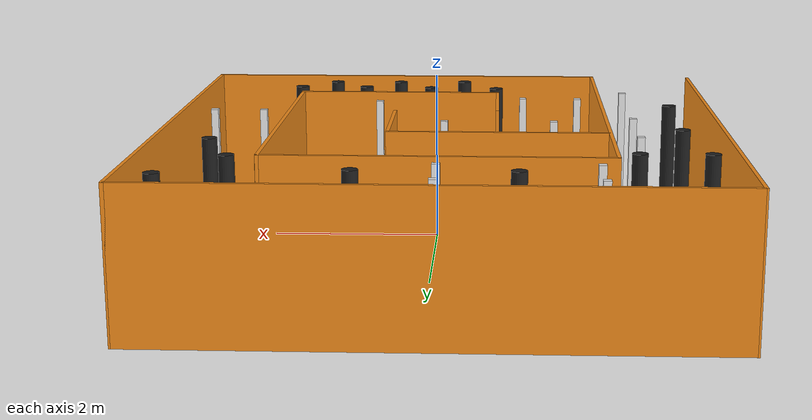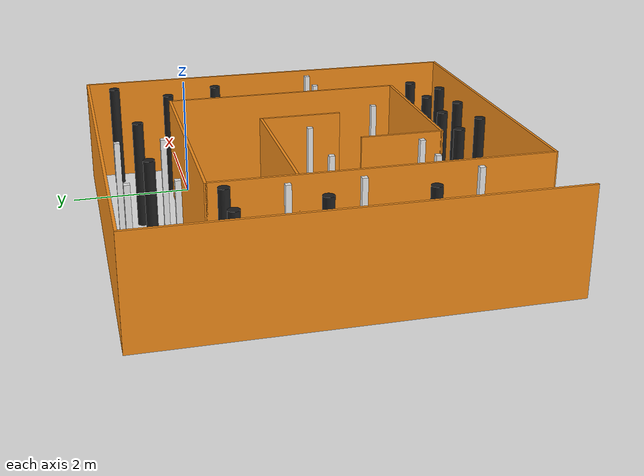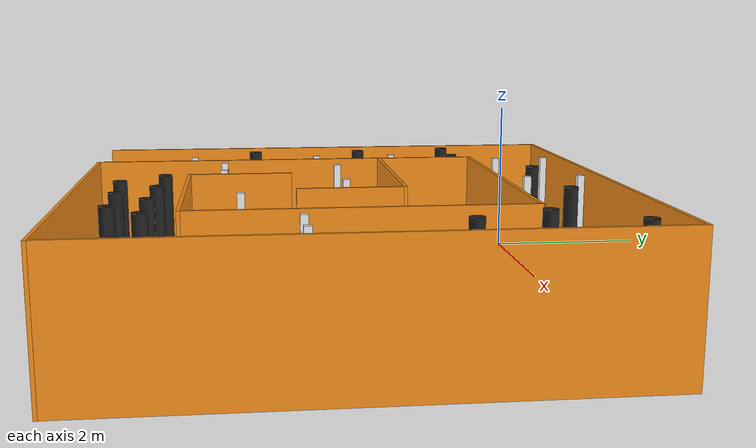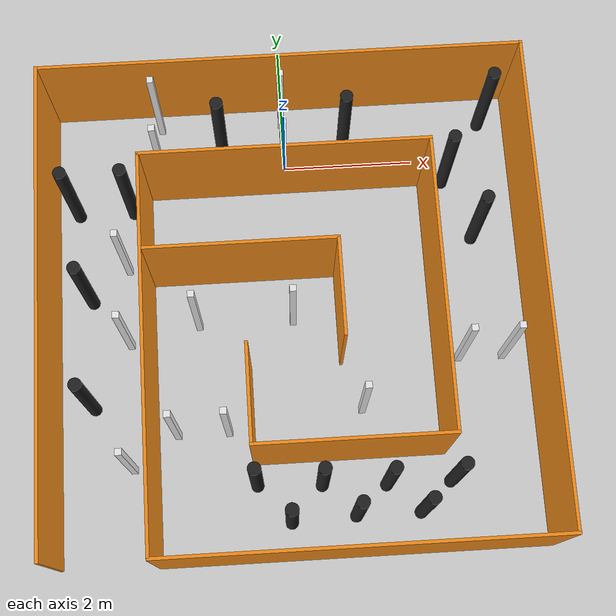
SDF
<?xml version='1.0'?>
<sdf version='1.7'>
  <model name='pesu_hackathon_arena_1'>
    <link name='link_0'>
      <pose>0 0 0 0 -0 0</pose>
      <self_collide>0</self_collide>
      <enable_wind>0</enable_wind>
      <kinematic>0</kinematic>
      <visual name='visual'>
        <pose>0 0 0 0 -0 0</pose>
        <geometry>
          <box>
            <size>4.5 0.05 2</size>
          </box>
        </geometry>
        <material>
          <lighting>1</lighting>
          <script>
            <uri>file://media/materials/scripts/gazebo.material</uri>
            <name>Gazebo/Orange</name>
          </script>
          <shader type='pixel'/>
        </material>
        <transparency>0</transparency>
        <cast_shadows>1</cast_shadows>
      </visual>
      <collision name='collision'>
        <laser_retro>0</laser_retro>
        <max_contacts>10</max_contacts>
        <pose>0 0 0 0 -0 0</pose>
        <geometry>
          <box>
            <size>4.5 0.05 2</size>
          </box>
        </geometry>
        <surface>
          <friction>
            <ode>
              <mu>1</mu>
              <mu2>1</mu2>
              <fdir1>0 0 0</fdir1>
              <slip1>0</slip1>
              <slip2>0</slip2>
            </ode>
            <torsional>
              <coefficient>1</coefficient>
              <patch_radius>0</patch_radius>
              <surface_radius>0</surface_radius>
              <use_patch_radius>1</use_patch_radius>
              <ode>
                <slip>0</slip>
              </ode>
            </torsional>
          </friction>
          <bounce>
            <restitution_coefficient>0</restitution_coefficient>
            <threshold>1e+06</threshold>
          </bounce>
          <contact>
            <collide_without_contact>0</collide_without_contact>
            <collide_without_contact_bitmask>1</collide_without_contact_bitmask>
            <collide_bitmask>1</collide_bitmask>
            <ode>
              <soft_cfm>0</soft_cfm>
              <soft_erp>0.2</soft_erp>
              <kp>1e+13</kp>
              <kd>1</kd>
              <max_vel>0.01</max_vel>
              <min_depth>0</min_depth>
            </ode>
            <bullet>
              <split_impulse>1</split_impulse>
              <split_impulse_penetration_threshold>-0.01</split_impulse_penetration_threshold>
              <soft_cfm>0</soft_cfm>
              <soft_erp>0.2</soft_erp>
              <kp>1e+13</kp>
              <kd>1</kd>
            </bullet>
          </contact>
        </surface>
      </collision>
    </link>

    <link name='link_1'>

      <pose>0 1.5 0 0 -0 0</pose>
      <self_collide>0</self_collide>
      <enable_wind>0</enable_wind>
      <kinematic>0</kinematic>`
      <visual name='visual'>
        <pose>0 0 0 0 -0 0</pose>
        <geometry>
          <box>
            <size>7.5 0.05 2</size>
          </box>
        </geometry>
        <material>
          <lighting>1</lighting>
          <script>
            <uri>file://media/materials/scripts/gazebo.material</uri>
            <name>Gazebo/Orange</name>
          </script>
          <shader type='pixel'/>
        </material>
        <transparency>0</transparency>
        <cast_shadows>1</cast_shadows>
      </visual>
      <collision name='collision'>
        <laser_retro>0</laser_retro>
        <max_contacts>10</max_contacts>
        <pose>0 0 0 0 -0 0</pose>
        <geometry>
          <box>
            <size>7.5 0.05 2</size>
          </box>
        </geometry>
        <surface>
          <friction>
            <ode>
              <mu>1</mu>
              <mu2>1</mu2>
              <fdir1>0 0 0</fdir1>
              <slip1>0</slip1>
              <slip2>0</slip2>
            </ode>
            <torsional>
              <coefficient>1</coefficient>
              <patch_radius>0</patch_radius>
              <surface_radius>0</surface_radius>
              <use_patch_radius>1</use_patch_radius>
              <ode>
                <slip>0</slip>
              </ode>
            </torsional>
          </friction>
          <bounce>
            <restitution_coefficient>0</restitution_coefficient>
            <threshold>1e+06</threshold>
          </bounce>
          <contact>
            <collide_without_contact>0</collide_without_contact>
            <collide_without_contact_bitmask>1</collide_without_contact_bitmask>
            <collide_bitmask>1</collide_bitmask>
            <ode>
              <soft_cfm>0</soft_cfm>
              <soft_erp>0.2</soft_erp>
              <kp>1e+13</kp>
              <kd>1</kd>
              <max_vel>0.01</max_vel>
              <min_depth>0</min_depth>
            </ode>
            <bullet>
              <split_impulse>1</split_impulse>
              <split_impulse_penetration_threshold>-0.01</split_impulse_penetration_threshold>
              <soft_cfm>0</soft_cfm>
              <soft_erp>0.2</soft_erp>
              <kp>1e+13</kp>
              <kd>1</kd>
            </bullet>
          </contact>
        </surface>
      </collision>
    </link>

    <link name='link_2'>

      <pose>-2.225 -3 0 0 -0 0</pose>
      <self_collide>0</self_collide>
      <enable_wind>0</enable_wind>
      <kinematic>0</kinematic>
      <visual name='visual'>
        <pose>0 0 0 0 -0 0</pose>
        <geometry>
          <box>
            <size>0.05 6 2</size>
          </box>
        </geometry>
        <material>
          <lighting>1</lighting>
          <script>
            <uri>file://media/materials/scripts/gazebo.material</uri>
            <name>Gazebo/Orange</name>
          </script>
          <shader type='pixel'/>
        </material>
        <transparency>0</transparency>
        <cast_shadows>1</cast_shadows>
      </visual>
      <collision name='collision'>
        <laser_retro>0</laser_retro>
        <max_contacts>10</max_contacts>
        <pose>0 0 0 0 -0 0</pose>
        <geometry>
          <box>
            <size>0.05 6 2</size>
          </box>
        </geometry>
        <surface>
          <friction>
            <ode>
              <mu>1</mu>
              <mu2>1</mu2>
              <fdir1>0 0 0</fdir1>
              <slip1>0</slip1>
              <slip2>0</slip2>
            </ode>
            <torsional>
              <coefficient>1</coefficient>
              <patch_radius>0</patch_radius>
              <surface_radius>0</surface_radius>
              <use_patch_radius>1</use_patch_radius>
              <ode>
                <slip>0</slip>
              </ode>
            </torsional>
          </friction>
          <bounce>
            <restitution_coefficient>0</restitution_coefficient>
            <threshold>1e+06</threshold>
          </bounce>
          <contact>
            <collide_without_contact>0</collide_without_contact>
            <collide_without_contact_bitmask>1</collide_without_contact_bitmask>
            <collide_bitmask>1</collide_bitmask>
            <ode>
              <soft_cfm>0</soft_cfm>
              <soft_erp>0.2</soft_erp>
              <kp>1e+13</kp>
              <kd>1</kd>
              <max_vel>0.01</max_vel>
              <min_depth>0</min_depth>
            </ode>
            <bullet>
              <split_impulse>1</split_impulse>
              <split_impulse_penetration_threshold>-0.01</split_impulse_penetration_threshold>
              <soft_cfm>0</soft_cfm>
              <soft_erp>0.2</soft_erp>
              <kp>1e+13</kp>
              <kd>1</kd>
            </bullet>
          </contact>
        </surface>
      </collision>
    </link>

    <link name='link_3'>

      <pose>2.225 -2.225 0 0 -0 0</pose>
      <self_collide>0</self_collide>
      <enable_wind>0</enable_wind>
      <kinematic>0</kinematic>
      <visual name='visual'>
        <pose>0 0 0 0 -0 0</pose>
        <geometry>
          <box>
            <size>0.05 4.5 2</size>
          </box>
        </geometry>
        <material>
          <lighting>1</lighting>
          <script>
            <uri>file://media/materials/scripts/gazebo.material</uri>
            <name>Gazebo/Orange</name>
          </script>
          <shader type='pixel'/>
        </material>
        <transparency>0</transparency>
        <cast_shadows>1</cast_shadows>
      </visual>
      <collision name='collision'>
        <laser_retro>0</laser_retro>
        <max_contacts>10</max_contacts>
        <pose>0 0 0 0 -0 0</pose>
        <geometry>
          <box>
            <size>0.05 4.5 2</size>
          </box>
        </geometry>
        <surface>
          <friction>
            <ode>
              <mu>1</mu>
              <mu2>1</mu2>
              <fdir1>0 0 0</fdir1>
              <slip1>0</slip1>
              <slip2>0</slip2>
            </ode>
            <torsional>
              <coefficient>1</coefficient>
              <patch_radius>0</patch_radius>
              <surface_radius>0</surface_radius>
              <use_patch_radius>1</use_patch_radius>
              <ode>
                <slip>0</slip>
              </ode>
            </torsional>
          </friction>
          <bounce>
            <restitution_coefficient>0</restitution_coefficient>
            <threshold>1e+06</threshold>
          </bounce>
          <contact>
            <collide_without_contact>0</collide_without_contact>
            <collide_without_contact_bitmask>1</collide_without_contact_bitmask>
            <collide_bitmask>1</collide_bitmask>
            <ode>
              <soft_cfm>0</soft_cfm>
              <soft_erp>0.2</soft_erp>
              <kp>1e+13</kp>
              <kd>1</kd>
              <max_vel>0.01</max_vel>
              <min_depth>0</min_depth>
            </ode>
            <bullet>
              <split_impulse>1</split_impulse>
              <split_impulse_penetration_threshold>-0.01</split_impulse_penetration_threshold>
              <soft_cfm>0</soft_cfm>
              <soft_erp>0.2</soft_erp>
              <kp>1e+13</kp>
              <kd>1</kd>
            </bullet>
          </contact>
        </surface>
      </collision>
    </link>

    <link name='link_4'>

      <pose>-3.75 -2.225 0 0 -0 0</pose>
      <self_collide>0</self_collide>
      <enable_wind>0</enable_wind>
      <kinematic>0</kinematic>
      <visual name='visual'>
        <pose>0 0 0 0 -0 0</pose>
        <geometry>
          <box>
            <size>0.05 7.5 2</size>
          </box>
        </geometry>
        <material>
          <lighting>1</lighting>
          <script>
            <uri>file://media/materials/scripts/gazebo.material</uri>
            <name>Gazebo/Orange</name>
          </script>
          <shader type='pixel'/>
        </material>
        <transparency>0</transparency>
        <cast_shadows>1</cast_shadows>
      </visual>
      <collision name='collision'>
        <laser_retro>0</laser_retro>
        <max_contacts>10</max_contacts>
        <pose>0 0 0 0 -0 0</pose>
        <geometry>
          <box>
            <size>0.05 7.5 2</size>
          </box>
        </geometry>
        <surface>
          <friction>
            <ode>
              <mu>1</mu>
              <mu2>1</mu2>
              <fdir1>0 0 0</fdir1>
              <slip1>0</slip1>
              <slip2>0</slip2>
            </ode>
            <torsional>
              <coefficient>1</coefficient>
              <patch_radius>0</patch_radius>
              <surface_radius>0</surface_radius>
              <use_patch_radius>1</use_patch_radius>
              <ode>
                <slip>0</slip>
              </ode>
            </torsional>
          </friction>
          <bounce>
            <restitution_coefficient>0</restitution_coefficient>
            <threshold>1e+06</threshold>
          </bounce>
          <contact>
            <collide_without_contact>0</collide_without_contact>
            <collide_without_contact_bitmask>1</collide_without_contact_bitmask>
            <collide_bitmask>1</collide_bitmask>
            <ode>
              <soft_cfm>0</soft_cfm>
              <soft_erp>0.2</soft_erp>
              <kp>1e+13</kp>
              <kd>1</kd>
              <max_vel>0.01</max_vel>
              <min_depth>0</min_depth>
            </ode>
            <bullet>
              <split_impulse>1</split_impulse>
              <split_impulse_penetration_threshold>-0.01</split_impulse_penetration_threshold>
              <soft_cfm>0</soft_cfm>
              <soft_erp>0.2</soft_erp>
              <kp>1e+13</kp>
              <kd>1</kd>
            </bullet>
          </contact>
        </surface>
      </collision>
    </link>

    <link name='link_5'>

      <pose>3.75 -2.225 0 0 -0 0</pose>
      <self_collide>0</self_collide>
      <enable_wind>0</enable_wind>
      <kinematic>0</kinematic>
      <visual name='visual'>
        <pose>0 0 0 0 -0 0</pose>
        <geometry>
          <box>
            <size>0.05 7.5 2</size>
          </box>
        </geometry>
        <material>
          <lighting>1</lighting>
          <script>
            <uri>file://media/materials/scripts/gazebo.material</uri>
            <name>Gazebo/Orange</name>
          </script>
          <shader type='pixel'/>
        </material>
        <transparency>0</transparency>
        <cast_shadows>1</cast_shadows>
      </visual>
      <collision name='collision'>
        <laser_retro>0</laser_retro>
        <max_contacts>10</max_contacts>
        <pose>0 0 0 0 -0 0</pose>
        <geometry>
          <box>
            <size>0.05 7.5 2</size>
          </box>
        </geometry>
        <surface>
          <friction>
            <ode>
              <mu>1</mu>
              <mu2>1</mu2>
              <fdir1>0 0 0</fdir1>
              <slip1>0</slip1>
              <slip2>0</slip2>
            </ode>
            <torsional>
              <coefficient>1</coefficient>
              <patch_radius>0</patch_radius>
              <surface_radius>0</surface_radius>
              <use_patch_radius>1</use_patch_radius>
              <ode>
                <slip>0</slip>
              </ode>
            </torsional>
          </friction>
          <bounce>
            <restitution_coefficient>0</restitution_coefficient>
            <threshold>1e+06</threshold>
          </bounce>
          <contact>
            <collide_without_contact>0</collide_without_contact>
            <collide_without_contact_bitmask>1</collide_without_contact_bitmask>
            <collide_bitmask>1</collide_bitmask>
            <ode>
              <soft_cfm>0</soft_cfm>
              <soft_erp>0.2</soft_erp>
              <kp>1e+13</kp>
              <kd>1</kd>
              <max_vel>0.01</max_vel>
              <min_depth>0</min_depth>
            </ode>
            <bullet>
              <split_impulse>1</split_impulse>
              <split_impulse_penetration_threshold>-0.01</split_impulse_penetration_threshold>
              <soft_cfm>0</soft_cfm>
              <soft_erp>0.2</soft_erp>
              <kp>1e+13</kp>
              <kd>1</kd>
            </bullet>
          </contact>
        </surface>
      </collision>
    </link>

    <link name='link_6'>

      <pose>0.765 -6 0 0 -0 0</pose>
      <self_collide>0</self_collide>
      <enable_wind>0</enable_wind>
      <kinematic>0</kinematic>
      <visual name='visual'>
        <pose>0 0 0 0 -0 0</pose>
        <geometry>
          <box>
            <size>6.025 0.05 2</size>
          </box>
        </geometry>
        <material>
          <lighting>1</lighting>
          <script>
            <uri>file://media/materials/scripts/gazebo.material</uri>
            <name>Gazebo/Orange</name>
          </script>
          <shader type='pixel'/>
        </material>
        <transparency>0</transparency>
        <cast_shadows>1</cast_shadows>
      </visual>
      <collision name='collision'>
        <laser_retro>0</laser_retro>
        <max_contacts>10</max_contacts>
        <pose>0 0 0 0 -0 0</pose>
        <geometry>
          <box>
            <size>6.025 0.05 2</size>
          </box>
        </geometry>
        <surface>
          <friction>
            <ode>
              <mu>1</mu>
              <mu2>1</mu2>
              <fdir1>0 0 0</fdir1>
              <slip1>0</slip1>
              <slip2>0</slip2>
            </ode>
            <torsional>
              <coefficient>1</coefficient>
              <patch_radius>0</patch_radius>
              <surface_radius>0</surface_radius>
              <use_patch_radius>1</use_patch_radius>
              <ode>
                <slip>0</slip>
              </ode>
            </torsional>
          </friction>
          <bounce>
            <restitution_coefficient>0</restitution_coefficient>
            <threshold>1e+06</threshold>
          </bounce>
          <contact>
            <collide_without_contact>0</collide_without_contact>
            <collide_without_contact_bitmask>1</collide_without_contact_bitmask>
            <collide_bitmask>1</collide_bitmask>
            <ode>
              <soft_cfm>0</soft_cfm>
              <soft_erp>0.2</soft_erp>
              <kp>1e+13</kp>
              <kd>1</kd>
              <max_vel>0.01</max_vel>
              <min_depth>0</min_depth>
            </ode>
            <bullet>
              <split_impulse>1</split_impulse>
              <split_impulse_penetration_threshold>-0.01</split_impulse_penetration_threshold>
              <soft_cfm>0</soft_cfm>
              <soft_erp>0.2</soft_erp>
              <kp>1e+13</kp>
              <kd>1</kd>
            </bullet>
          </contact>
        </surface>
      </collision>
    </link>

    <link name='link_7'>

      <pose>-0.75 -1.5 0 0 -0 0</pose>
      <self_collide>0</self_collide>
      <enable_wind>0</enable_wind>
      <kinematic>0</kinematic>
      <visual name='visual'>
        <pose>0 0 0 0 -0 0</pose>
        <geometry>
          <box>
            <size>3 0.05 2</size>
          </box>
        </geometry>
        <material>
          <lighting>1</lighting>
          <script>
            <uri>file://media/materials/scripts/gazebo.material</uri>
            <name>Gazebo/Orange</name>
          </script>
          <shader type='pixel'/>
        </material>
        <transparency>0</transparency>
        <cast_shadows>1</cast_shadows>
      </visual>
      <collision name='collision'>
        <laser_retro>0</laser_retro>
        <max_contacts>10</max_contacts>
        <pose>0 0 0 0 -0 0</pose>
        <geometry>
          <box>
            <size>3 0.05 2</size>
          </box>
        </geometry>
        <surface>
          <friction>
            <ode>
              <mu>1</mu>
              <mu2>1</mu2>
              <fdir1>0 0 0</fdir1>
              <slip1>0</slip1>
              <slip2>0</slip2>
            </ode>
            <torsional>
              <coefficient>1</coefficient>
              <patch_radius>0</patch_radius>
              <surface_radius>0</surface_radius>
              <use_patch_radius>1</use_patch_radius>
              <ode>
                <slip>0</slip>
              </ode>
            </torsional>
          </friction>
          <bounce>
            <restitution_coefficient>0</restitution_coefficient>
            <threshold>1e+06</threshold>
          </bounce>
          <contact>
            <collide_without_contact>0</collide_without_contact>
            <collide_without_contact_bitmask>1</collide_without_contact_bitmask>
            <collide_bitmask>1</collide_bitmask>
            <ode>
              <soft_cfm>0</soft_cfm>
              <soft_erp>0.2</soft_erp>
              <kp>1e+13</kp>
              <kd>1</kd>
              <max_vel>0.01</max_vel>
              <min_depth>0</min_depth>
            </ode>
            <bullet>
              <split_impulse>1</split_impulse>
              <split_impulse_penetration_threshold>-0.01</split_impulse_penetration_threshold>
              <soft_cfm>0</soft_cfm>
              <soft_erp>0.2</soft_erp>
              <kp>1e+13</kp>
              <kd>1</kd>
            </bullet>
          </contact>
        </surface>
      </collision>
    </link>

    <link name='link_8'>

      <pose>0.75 -4.5 0 0 -0 0</pose>
      <self_collide>0</self_collide>
      <enable_wind>0</enable_wind>
      <kinematic>0</kinematic>
      <visual name='visual'>
        <pose>0 0 0 0 -0 0</pose>
        <geometry>
          <box>
            <size>3 0.05 2</size>
          </box>
        </geometry>
        <material>
          <lighting>1</lighting>
          <script>
            <uri>file://media/materials/scripts/gazebo.material</uri>
            <name>Gazebo/Orange</name>
          </script>
          <shader type='pixel'/>
        </material>
        <transparency>0</transparency>
        <cast_shadows>1</cast_shadows>
      </visual>
      <collision name='collision'>
        <laser_retro>0</laser_retro>
        <max_contacts>10</max_contacts>
        <pose>0 0 0 0 -0 0</pose>
        <geometry>
          <box>
            <size>3 0.05 2</size>
          </box>
        </geometry>
        <surface>
          <friction>
            <ode>
              <mu>1</mu>
              <mu2>1</mu2>
              <fdir1>0 0 0</fdir1>
              <slip1>0</slip1>
              <slip2>0</slip2>
            </ode>
            <torsional>
              <coefficient>1</coefficient>
              <patch_radius>0</patch_radius>
              <surface_radius>0</surface_radius>
              <use_patch_radius>1</use_patch_radius>
              <ode>
                <slip>0</slip>
              </ode>
            </torsional>
          </friction>
          <bounce>
            <restitution_coefficient>0</restitution_coefficient>
            <threshold>1e+06</threshold>
          </bounce>
          <contact>
            <collide_without_contact>0</collide_without_contact>
            <collide_without_contact_bitmask>1</collide_without_contact_bitmask>
            <collide_bitmask>1</collide_bitmask>
            <ode>
              <soft_cfm>0</soft_cfm>
              <soft_erp>0.2</soft_erp>
              <kp>1e+13</kp>
              <kd>1</kd>
              <max_vel>0.01</max_vel>
              <min_depth>0</min_depth>
            </ode>
            <bullet>
              <split_impulse>1</split_impulse>
              <split_impulse_penetration_threshold>-0.01</split_impulse_penetration_threshold>
              <soft_cfm>0</soft_cfm>
              <soft_erp>0.2</soft_erp>
              <kp>1e+13</kp>
              <kd>1</kd>
            </bullet>
          </contact>
        </surface>
      </collision>
    </link>

    <link name='link_9'>

      <pose>0.725 -2.25 0 0 -0 0</pose>
      <self_collide>0</self_collide>
      <enable_wind>0</enable_wind>
      <kinematic>0</kinematic>
      <visual name='visual'>
        <pose>0 0 0 0 -0 0</pose>
        <geometry>
          <box>
            <size>0.05 1.5 2</size>
          </box>
        </geometry>
        <material>
          <lighting>1</lighting>
          <script>
            <uri>file://media/materials/scripts/gazebo.material</uri>
            <name>Gazebo/Orange</name>
          </script>
          <shader type='pixel'/>
        </material>
        <transparency>0</transparency>
        <cast_shadows>1</cast_shadows>
      </visual>
      <collision name='collision'>
        <laser_retro>0</laser_retro>
        <max_contacts>10</max_contacts>
        <pose>0 0 0 0 -0 0</pose>
        <geometry>
          <box>
            <size>0.05 1.5 2</size>
          </box>
        </geometry>
        <surface>
          <friction>
            <ode>
              <mu>1</mu>
              <mu2>1</mu2>
              <fdir1>0 0 0</fdir1>
              <slip1>0</slip1>
              <slip2>0</slip2>
            </ode>
            <torsional>
              <coefficient>1</coefficient>
              <patch_radius>0</patch_radius>
              <surface_radius>0</surface_radius>
              <use_patch_radius>1</use_patch_radius>
              <ode>
                <slip>0</slip>
              </ode>
            </torsional>
          </friction>
          <bounce>
            <restitution_coefficient>0</restitution_coefficient>
            <threshold>1e+06</threshold>
          </bounce>
          <contact>
            <collide_without_contact>0</collide_without_contact>
            <collide_without_contact_bitmask>1</collide_without_contact_bitmask>
            <collide_bitmask>1</collide_bitmask>
            <ode>
              <soft_cfm>0</soft_cfm>
              <soft_erp>0.2</soft_erp>
              <kp>1e+13</kp>
              <kd>1</kd>
              <max_vel>0.01</max_vel>
              <min_depth>0</min_depth>
            </ode>
            <bullet>
              <split_impulse>1</split_impulse>
              <split_impulse_penetration_threshold>-0.01</split_impulse_penetration_threshold>
              <soft_cfm>0</soft_cfm>
              <soft_erp>0.2</soft_erp>
              <kp>1e+13</kp>
              <kd>1</kd>
            </bullet>
          </contact>
        </surface>
      </collision>
    </link>

     <link name='link_10'>

      <pose>-0.725 -3.75 0 0 -0 0</pose>
      <self_collide>0</self_collide>
      <enable_wind>0</enable_wind>
      <kinematic>0</kinematic>
      <visual name='visual'>
        <pose>0 0 0 0 -0 0</pose>
        <geometry>
          <box>
            <size>0.05 1.5 2</size>
          </box>
        </geometry>
        <material>
          <lighting>1</lighting>
          <script>
            <uri>file://media/materials/scripts/gazebo.material</uri>
            <name>Gazebo/Orange</name>
          </script>
          <shader type='pixel'/>
        </material>
        <transparency>0</transparency>
        <cast_shadows>1</cast_shadows>
      </visual>
      <collision name='collision'>
        <laser_retro>0</laser_retro>
        <max_contacts>10</max_contacts>
        <pose>0 0 0 0 -0 0</pose>
        <geometry>
          <box>
            <size>0.05 1.5 2</size>
          </box>
        </geometry>
        <surface>
          <friction>
            <ode>
              <mu>1</mu>
              <mu2>1</mu2>
              <fdir1>0 0 0</fdir1>
              <slip1>0</slip1>
              <slip2>0</slip2>
            </ode>
            <torsional>
              <coefficient>1</coefficient>
              <patch_radius>0</patch_radius>
              <surface_radius>0</surface_radius>
              <use_patch_radius>1</use_patch_radius>
              <ode>
                <slip>0</slip>
              </ode>
            </torsional>
          </friction>
          <bounce>
            <restitution_coefficient>0</restitution_coefficient>
            <threshold>1e+06</threshold>
          </bounce>
          <contact>
            <collide_without_contact>0</collide_without_contact>
            <collide_without_contact_bitmask>1</collide_without_contact_bitmask>
            <collide_bitmask>1</collide_bitmask>
            <ode>
              <soft_cfm>0</soft_cfm>
              <soft_erp>0.2</soft_erp>
              <kp>1e+13</kp>
              <kd>1</kd>
              <max_vel>0.01</max_vel>
              <min_depth>0</min_depth>
            </ode>
            <bullet>
              <split_impulse>1</split_impulse>
              <split_impulse_penetration_threshold>-0.01</split_impulse_penetration_threshold>
              <soft_cfm>0</soft_cfm>
              <soft_erp>0.2</soft_erp>
              <kp>1e+13</kp>
              <kd>1</kd>
            </bullet>
          </contact>
        </surface>
      </collision>
    </link>

    <link name='obstacle_0'>

      <pose>1 -3.75 0 0 -0 0</pose>
      <self_collide>0</self_collide>
      <enable_wind>0</enable_wind>
      <kinematic>0</kinematic>
      <visual name='visual'>
        <pose>0 0 0 0 -0 0</pose>
        <geometry>
          <box>
            <size>0.1 0.1 2</size>
          </box>
        </geometry>
        <material>
          <lighting>1</lighting>
          <script>
            <uri>file://media/materials/scripts/gazebo.material</uri>
            <name>Gazebo/White</name>
          </script>
          <shader type='pixel'/>
        </material>
        <transparency>0</transparency>
        <cast_shadows>1</cast_shadows>
      </visual>
      <collision name='collision'>
        <laser_retro>0</laser_retro>
        <max_contacts>10</max_contacts>
        <pose>0 0 0 0 -0 0</pose>
        <geometry>
          <box>
            <size>0.1 0.1 2</size>
          </box>
        </geometry>
        <surface>
          <friction>
            <ode>
              <mu>1</mu>
              <mu2>1</mu2>
              <fdir1>0 0 0</fdir1>
              <slip1>0</slip1>
              <slip2>0</slip2>
            </ode>
            <torsional>
              <coefficient>1</coefficient>
              <patch_radius>0</patch_radius>
              <surface_radius>0</surface_radius>
              <use_patch_radius>1</use_patch_radius>
              <ode>
                <slip>0</slip>
              </ode>
            </torsional>
          </friction>
          <bounce>
            <restitution_coefficient>0</restitution_coefficient>
            <threshold>1e+06</threshold>
          </bounce>
          <contact>
            <collide_without_contact>0</collide_without_contact>
            <collide_without_contact_bitmask>1</collide_without_contact_bitmask>
            <collide_bitmask>1</collide_bitmask>
            <ode>
              <soft_cfm>0</soft_cfm>
              <soft_erp>0.2</soft_erp>
              <kp>1e+13</kp>
              <kd>1</kd>
              <max_vel>0.01</max_vel>
              <min_depth>0</min_depth>
            </ode>
            <bullet>
              <split_impulse>1</split_impulse>
              <split_impulse_penetration_threshold>-0.01</split_impulse_penetration_threshold>
              <soft_cfm>0</soft_cfm>
              <soft_erp>0.2</soft_erp>
              <kp>1e+13</kp>
              <kd>1</kd>
            </bullet>
          </contact>
        </surface>
      </collision>
    </link>

    <link name='obstacle_1'>

      <pose>0 -2.25 0 0 -0 0</pose>
      <self_collide>0</self_collide>
      <enable_wind>0</enable_wind>
      <kinematic>0</kinematic>
      <visual name='visual'>
        <pose>0 0 0 0 -0 0</pose>
        <geometry>
          <box>
            <size>0.1 0.1 2</size>
          </box>
        </geometry>
        <material>
          <lighting>1</lighting>
          <script>
            <uri>file://media/materials/scripts/gazebo.material</uri>
            <name>Gazebo/White</name>
          </script>
          <shader type='pixel'/>
        </material>
        <transparency>0</transparency>
        <cast_shadows>1</cast_shadows>
      </visual>
      <collision name='collision'>
        <laser_retro>0</laser_retro>
        <max_contacts>10</max_contacts>
        <pose>0 0 0 0 -0 0</pose>
        <geometry>
          <box>
            <size>0.1 0.1 2</size>
          </box>
        </geometry>
        <surface>
          <friction>
            <ode>
              <mu>1</mu>
              <mu2>1</mu2>
              <fdir1>0 0 0</fdir1>
              <slip1>0</slip1>
              <slip2>0</slip2>
            </ode>
            <torsional>
              <coefficient>1</coefficient>
              <patch_radius>0</patch_radius>
              <surface_radius>0</surface_radius>
              <use_patch_radius>1</use_patch_radius>
              <ode>
                <slip>0</slip>
              </ode>
            </torsional>
          </friction>
          <bounce>
            <restitution_coefficient>0</restitution_coefficient>
            <threshold>1e+06</threshold>
          </bounce>
          <contact>
            <collide_without_contact>0</collide_without_contact>
            <collide_without_contact_bitmask>1</collide_without_contact_bitmask>
            <collide_bitmask>1</collide_bitmask>
            <ode>
              <soft_cfm>0</soft_cfm>
              <soft_erp>0.2</soft_erp>
              <kp>1e+13</kp>
              <kd>1</kd>
              <max_vel>0.01</max_vel>
              <min_depth>0</min_depth>
            </ode>
            <bullet>
              <split_impulse>1</split_impulse>
              <split_impulse_penetration_threshold>-0.01</split_impulse_penetration_threshold>
              <soft_cfm>0</soft_cfm>
              <soft_erp>0.2</soft_erp>
              <kp>1e+13</kp>
              <kd>1</kd>
            </bullet>
          </contact>
        </surface>
      </collision>
    </link>

    <link name='obstacle_2'>

      <pose>-1.5 -2.25 0 0 -0 0</pose>
      <self_collide>0</self_collide>
      <enable_wind>0</enable_wind>
      <kinematic>0</kinematic>
      <visual name='visual'>
        <pose>0 0 0 0 -0 0</pose>
        <geometry>
          <box>
            <size>0.1 0.1 2</size>
          </box>
        </geometry>
        <material>
          <lighting>1</lighting>
          <script>
            <uri>file://media/materials/scripts/gazebo.material</uri>
            <name>Gazebo/White</name>
          </script>
          <shader type='pixel'/>
        </material>
        <transparency>0</transparency>
        <cast_shadows>1</cast_shadows>
      </visual>
      <collision name='collision'>
        <laser_retro>0</laser_retro>
        <max_contacts>10</max_contacts>
        <pose>0 0 0 0 -0 0</pose>
        <geometry>
          <box>
            <size>0.1 0.1 2</size>
          </box>
        </geometry>
        <surface>
          <friction>
            <ode>
              <mu>1</mu>
              <mu2>1</mu2>
              <fdir1>0 0 0</fdir1>
              <slip1>0</slip1>
              <slip2>0</slip2>
            </ode>
            <torsional>
              <coefficient>1</coefficient>
              <patch_radius>0</patch_radius>
              <surface_radius>0</surface_radius>
              <use_patch_radius>1</use_patch_radius>
              <ode>
                <slip>0</slip>
              </ode>
            </torsional>
          </friction>
          <bounce>
            <restitution_coefficient>0</restitution_coefficient>
            <threshold>1e+06</threshold>
          </bounce>
          <contact>
            <collide_without_contact>0</collide_without_contact>
            <collide_without_contact_bitmask>1</collide_without_contact_bitmask>
            <collide_bitmask>1</collide_bitmask>
            <ode>
              <soft_cfm>0</soft_cfm>
              <soft_erp>0.2</soft_erp>
              <kp>1e+13</kp>
              <kd>1</kd>
              <max_vel>0.01</max_vel>
              <min_depth>0</min_depth>
            </ode>
            <bullet>
              <split_impulse>1</split_impulse>
              <split_impulse_penetration_threshold>-0.01</split_impulse_penetration_threshold>
              <soft_cfm>0</soft_cfm>
              <soft_erp>0.2</soft_erp>
              <kp>1e+13</kp>
              <kd>1</kd>
            </bullet>
          </contact>
        </surface>
      </collision>
    </link>

    <link name='obstacle_3'>

      <pose>-1.1 -4 0 0 -0 0</pose>
      <self_collide>0</self_collide>
      <enable_wind>0</enable_wind>
      <kinematic>0</kinematic>
      <visual name='visual'>
        <pose>0 0 0 0 -0 0</pose>
        <geometry>
          <box>
            <size>0.1 0.1 2</size>
          </box>
        </geometry>
        <material>
          <lighting>1</lighting>
          <script>
            <uri>file://media/materials/scripts/gazebo.material</uri>
            <name>Gazebo/White</name>
          </script>
          <shader type='pixel'/>
        </material>
        <transparency>0</transparency>
        <cast_shadows>1</cast_shadows>
      </visual>
      <collision name='collision'>
        <laser_retro>0</laser_retro>
        <max_contacts>10</max_contacts>
        <pose>0 0 0 0 -0 0</pose>
        <geometry>
          <box>
            <size>0.1 0.1 2</size>
          </box>
        </geometry>
        <surface>
          <friction>
            <ode>
              <mu>1</mu>
              <mu2>1</mu2>
              <fdir1>0 0 0</fdir1>
              <slip1>0</slip1>
              <slip2>0</slip2>
            </ode>
            <torsional>
              <coefficient>1</coefficient>
              <patch_radius>0</patch_radius>
              <surface_radius>0</surface_radius>
              <use_patch_radius>1</use_patch_radius>
              <ode>
                <slip>0</slip>
              </ode>
            </torsional>
          </friction>
          <bounce>
            <restitution_coefficient>0</restitution_coefficient>
            <threshold>1e+06</threshold>
          </bounce>
          <contact>
            <collide_without_contact>0</collide_without_contact>
            <collide_without_contact_bitmask>1</collide_without_contact_bitmask>
            <collide_bitmask>1</collide_bitmask>
            <ode>
              <soft_cfm>0</soft_cfm>
              <soft_erp>0.2</soft_erp>
              <kp>1e+13</kp>
              <kd>1</kd>
              <max_vel>0.01</max_vel>
              <min_depth>0</min_depth>
            </ode>
            <bullet>
              <split_impulse>1</split_impulse>
              <split_impulse_penetration_threshold>-0.01</split_impulse_penetration_threshold>
              <soft_cfm>0</soft_cfm>
              <soft_erp>0.2</soft_erp>
              <kp>1e+13</kp>
              <kd>1</kd>
            </bullet>
          </contact>
        </surface>
      </collision>
    </link>

    <link name='obstacle_4'>

      <pose>-1.9 -4 0 0 -0 0</pose>
      <self_collide>0</self_collide>
      <enable_wind>0</enable_wind>
      <kinematic>0</kinematic>
      <visual name='visual'>
        <pose>0 0 0 0 -0 0</pose>
        <geometry>
          <box>
            <size>0.1 0.1 2</size>
          </box>
        </geometry>
        <material>
          <lighting>1</lighting>
          <script>
            <uri>file://media/materials/scripts/gazebo.material</uri>
            <name>Gazebo/White</name>
          </script>
          <shader type='pixel'/>
        </material>
        <transparency>0</transparency>
        <cast_shadows>1</cast_shadows>
      </visual>
      <collision name='collision'>
        <laser_retro>0</laser_retro>
        <max_contacts>10</max_contacts>
        <pose>0 0 0 0 -0 0</pose>
        <geometry>
          <box>
            <size>0.1 0.1 2</size>
          </box>
        </geometry>
        <surface>
          <friction>
            <ode>
              <mu>1</mu>
              <mu2>1</mu2>
              <fdir1>0 0 0</fdir1>
              <slip1>0</slip1>
              <slip2>0</slip2>
            </ode>
            <torsional>
              <coefficient>1</coefficient>
              <patch_radius>0</patch_radius>
              <surface_radius>0</surface_radius>
              <use_patch_radius>1</use_patch_radius>
              <ode>
                <slip>0</slip>
              </ode>
            </torsional>
          </friction>
          <bounce>
            <restitution_coefficient>0</restitution_coefficient>
            <threshold>1e+06</threshold>
          </bounce>
          <contact>
            <collide_without_contact>0</collide_without_contact>
            <collide_without_contact_bitmask>1</collide_without_contact_bitmask>
            <collide_bitmask>1</collide_bitmask>
            <ode>
              <soft_cfm>0</soft_cfm>
              <soft_erp>0.2</soft_erp>
              <kp>1e+13</kp>
              <kd>1</kd>
              <max_vel>0.01</max_vel>
              <min_depth>0</min_depth>
            </ode>
            <bullet>
              <split_impulse>1</split_impulse>
              <split_impulse_penetration_threshold>-0.01</split_impulse_penetration_threshold>
              <soft_cfm>0</soft_cfm>
              <soft_erp>0.2</soft_erp>
              <kp>1e+13</kp>
              <kd>1</kd>
            </bullet>
          </contact>
        </surface>
      </collision>
    </link>

     <link name='obstacle_5'>

      <pose>-0.7 -4.85 0 0 -0 0</pose>
      <self_collide>0</self_collide>
      <enable_wind>0</enable_wind>
      <kinematic>0</kinematic>
      <visual name='visual'>
        <pose>0 0 0 0 -0 0</pose>
        <geometry>
          <cylinder>
            <radius>0.1</radius>
            <length>2</length>
          </cylinder>
        </geometry>
        <material>
          <lighting>1</lighting>
          <script>
            <uri>file://media/materials/scripts/gazebo.material</uri>
            <name>Gazebo/Black</name>
          </script>
          <shader type='pixel'/>
        </material>
        <transparency>0</transparency>
        <cast_shadows>1</cast_shadows>
      </visual>
      <collision name='collision'>
        <laser_retro>0</laser_retro>
        <max_contacts>10</max_contacts>
        <pose>0 0 0 0 -0 0</pose>
        <geometry>
          <cylinder>
            <radius>0.1</radius>
            <length>2</length>
          </cylinder>
        </geometry>
        <surface>
          <friction>
            <ode>
              <mu>1</mu>
              <mu2>1</mu2>
              <fdir1>0 0 0</fdir1>
              <slip1>0</slip1>
              <slip2>0</slip2>
            </ode>
            <torsional>
              <coefficient>1</coefficient>
              <patch_radius>0</patch_radius>
              <surface_radius>0</surface_radius>
              <use_patch_radius>1</use_patch_radius>
              <ode>
                <slip>0</slip>
              </ode>
            </torsional>
          </friction>
          <bounce>
            <restitution_coefficient>0</restitution_coefficient>
            <threshold>1e+06</threshold>
          </bounce>
          <contact>
            <collide_without_contact>0</collide_without_contact>
            <collide_without_contact_bitmask>1</collide_without_contact_bitmask>
            <collide_bitmask>1</collide_bitmask>
            <ode>
              <soft_cfm>0</soft_cfm>
              <soft_erp>0.2</soft_erp>
              <kp>1e+13</kp>
              <kd>1</kd>
              <max_vel>0.01</max_vel>
              <min_depth>0</min_depth>
            </ode>
            <bullet>
              <split_impulse>1</split_impulse>
              <split_impulse_penetration_threshold>-0.01</split_impulse_penetration_threshold>
              <soft_cfm>0</soft_cfm>
              <soft_erp>0.2</soft_erp>
              <kp>1e+13</kp>
              <kd>1</kd>
            </bullet>
          </contact>
        </surface>
      </collision>
    </link>

     <link name='obstacle_6'>

      <pose>-0.2 -5.45 0 0 -0 0</pose>
      <self_collide>0</self_collide>
      <enable_wind>0</enable_wind>
      <kinematic>0</kinematic>
      <visual name='visual'>
        <pose>0 0 0 0 -0 0</pose>
        <geometry>
          <cylinder>
            <radius>0.1</radius>
            <length>2</length>
          </cylinder>
        </geometry>
        <material>
          <lighting>1</lighting>
          <script>
            <uri>file://media/materials/scripts/gazebo.material</uri>
            <name>Gazebo/Black</name>
          </script>
          <shader type='pixel'/>
        </material>
        <transparency>0</transparency>
        <cast_shadows>1</cast_shadows>
      </visual>
      <collision name='collision'>
        <laser_retro>0</laser_retro>
        <max_contacts>10</max_contacts>
        <pose>0 0 0 0 -0 0</pose>
        <geometry>
          <cylinder>
            <radius>0.1</radius>
            <length>2</length>
          </cylinder>
        </geometry>
        <surface>
          <friction>
            <ode>
              <mu>1</mu>
              <mu2>1</mu2>
              <fdir1>0 0 0</fdir1>
              <slip1>0</slip1>
              <slip2>0</slip2>
            </ode>
            <torsional>
              <coefficient>1</coefficient>
              <patch_radius>0</patch_radius>
              <surface_radius>0</surface_radius>
              <use_patch_radius>1</use_patch_radius>
              <ode>
                <slip>0</slip>
              </ode>
            </torsional>
          </friction>
          <bounce>
            <restitution_coefficient>0</restitution_coefficient>
            <threshold>1e+06</threshold>
          </bounce>
          <contact>
            <collide_without_contact>0</collide_without_contact>
            <collide_without_contact_bitmask>1</collide_without_contact_bitmask>
            <collide_bitmask>1</collide_bitmask>
            <ode>
              <soft_cfm>0</soft_cfm>
              <soft_erp>0.2</soft_erp>
              <kp>1e+13</kp>
              <kd>1</kd>
              <max_vel>0.01</max_vel>
              <min_depth>0</min_depth>
            </ode>
            <bullet>
              <split_impulse>1</split_impulse>
              <split_impulse_penetration_threshold>-0.01</split_impulse_penetration_threshold>
              <soft_cfm>0</soft_cfm>
              <soft_erp>0.2</soft_erp>
              <kp>1e+13</kp>
              <kd>1</kd>
            </bullet>
          </contact>
        </surface>
      </collision>
    </link>

    <link name='obstacle_7'>

      <pose>0.3 -4.9 0 0 -0 0</pose>
      <self_collide>0</self_collide>
      <enable_wind>0</enable_wind>
      <kinematic>0</kinematic>
      <visual name='visual'>
        <pose>0 0 0 0 -0 0</pose>
        <geometry>
          <cylinder>
            <radius>0.1</radius>
            <length>2</length>
          </cylinder>
        </geometry>
        <material>
          <lighting>1</lighting>
          <script>
            <uri>file://media/materials/scripts/gazebo.material</uri>
            <name>Gazebo/Black</name>
          </script>
          <shader type='pixel'/>
        </material>
        <transparency>0</transparency>
        <cast_shadows>1</cast_shadows>
      </visual>
      <collision name='collision'>
        <laser_retro>0</laser_retro>
        <max_contacts>10</max_contacts>
        <pose>0 0 0 0 -0 0</pose>
        <geometry>
          <cylinder>
            <radius>0.1</radius>
            <length>2</length>
          </cylinder>
        </geometry>
        <surface>
          <friction>
            <ode>
              <mu>1</mu>
              <mu2>1</mu2>
              <fdir1>0 0 0</fdir1>
              <slip1>0</slip1>
              <slip2>0</slip2>
            </ode>
            <torsional>
              <coefficient>1</coefficient>
              <patch_radius>0</patch_radius>
              <surface_radius>0</surface_radius>
              <use_patch_radius>1</use_patch_radius>
              <ode>
                <slip>0</slip>
              </ode>
            </torsional>
          </friction>
          <bounce>
            <restitution_coefficient>0</restitution_coefficient>
            <threshold>1e+06</threshold>
          </bounce>
          <contact>
            <collide_without_contact>0</collide_without_contact>
            <collide_without_contact_bitmask>1</collide_without_contact_bitmask>
            <collide_bitmask>1</collide_bitmask>
            <ode>
              <soft_cfm>0</soft_cfm>
              <soft_erp>0.2</soft_erp>
              <kp>1e+13</kp>
              <kd>1</kd>
              <max_vel>0.01</max_vel>
              <min_depth>0</min_depth>
            </ode>
            <bullet>
              <split_impulse>1</split_impulse>
              <split_impulse_penetration_threshold>-0.01</split_impulse_penetration_threshold>
              <soft_cfm>0</soft_cfm>
              <soft_erp>0.2</soft_erp>
              <kp>1e+13</kp>
              <kd>1</kd>
            </bullet>
          </contact>
        </surface>
      </collision>
    </link>

     <link name='obstacle_8'>

      <pose>0.8 -5.4 0 0 -0 0</pose>
      <self_collide>0</self_collide>
      <enable_wind>0</enable_wind>
      <kinematic>0</kinematic>
      <visual name='visual'>
        <pose>0 0 0 0 -0 0</pose>
        <geometry>
          <cylinder>
            <radius>0.1</radius>
            <length>2</length>
          </cylinder>
        </geometry>
        <material>
          <lighting>1</lighting>
          <script>
            <uri>file://media/materials/scripts/gazebo.material</uri>
            <name>Gazebo/Black</name>
          </script>
          <shader type='pixel'/>
        </material>
        <transparency>0</transparency>
        <cast_shadows>1</cast_shadows>
      </visual>
      <collision name='collision'>
        <laser_retro>0</laser_retro>
        <max_contacts>10</max_contacts>
        <pose>0 0 0 0 -0 0</pose>
        <geometry>
          <cylinder>
            <radius>0.1</radius>
            <length>2</length>
          </cylinder>
        </geometry>
        <surface>
          <friction>
            <ode>
              <mu>1</mu>
              <mu2>1</mu2>
              <fdir1>0 0 0</fdir1>
              <slip1>0</slip1>
              <slip2>0</slip2>
            </ode>
            <torsional>
              <coefficient>1</coefficient>
              <patch_radius>0</patch_radius>
              <surface_radius>0</surface_radius>
              <use_patch_radius>1</use_patch_radius>
              <ode>
                <slip>0</slip>
              </ode>
            </torsional>
          </friction>
          <bounce>
            <restitution_coefficient>0</restitution_coefficient>
            <threshold>1e+06</threshold>
          </bounce>
          <contact>
            <collide_without_contact>0</collide_without_contact>
            <collide_without_contact_bitmask>1</collide_without_contact_bitmask>
            <collide_bitmask>1</collide_bitmask>
            <ode>
              <soft_cfm>0</soft_cfm>
              <soft_erp>0.2</soft_erp>
              <kp>1e+13</kp>
              <kd>1</kd>
              <max_vel>0.01</max_vel>
              <min_depth>0</min_depth>
            </ode>
            <bullet>
              <split_impulse>1</split_impulse>
              <split_impulse_penetration_threshold>-0.01</split_impulse_penetration_threshold>
              <soft_cfm>0</soft_cfm>
              <soft_erp>0.2</soft_erp>
              <kp>1e+13</kp>
              <kd>1</kd>
            </bullet>
          </contact>
        </surface>
      </collision>
    </link>

    <link name='obstacle_9'>

      <pose>1.3 -4.95 0 0 -0 0</pose>
      <self_collide>0</self_collide>
      <enable_wind>0</enable_wind>
      <kinematic>0</kinematic>
      <visual name='visual'>
        <pose>0 0 0 0 -0 0</pose>
        <geometry>
          <cylinder>
            <radius>0.1</radius>
            <length>2</length>
          </cylinder>
        </geometry>
        <material>
          <lighting>1</lighting>
          <script>
            <uri>file://media/materials/scripts/gazebo.material</uri>
            <name>Gazebo/Black</name>
          </script>
          <shader type='pixel'/>
        </material>
        <transparency>0</transparency>
        <cast_shadows>1</cast_shadows>
      </visual>
      <collision name='collision'>
        <laser_retro>0</laser_retro>
        <max_contacts>10</max_contacts>
        <pose>0 0 0 0 -0 0</pose>
        <geometry>
          <cylinder>
            <radius>0.1</radius>
            <length>2</length>
          </cylinder>
        </geometry>
        <surface>
          <friction>
            <ode>
              <mu>1</mu>
              <mu2>1</mu2>
              <fdir1>0 0 0</fdir1>
              <slip1>0</slip1>
              <slip2>0</slip2>
            </ode>
            <torsional>
              <coefficient>1</coefficient>
              <patch_radius>0</patch_radius>
              <surface_radius>0</surface_radius>
              <use_patch_radius>1</use_patch_radius>
              <ode>
                <slip>0</slip>
              </ode>
            </torsional>
          </friction>
          <bounce>
            <restitution_coefficient>0</restitution_coefficient>
            <threshold>1e+06</threshold>
          </bounce>
          <contact>
            <collide_without_contact>0</collide_without_contact>
            <collide_without_contact_bitmask>1</collide_without_contact_bitmask>
            <collide_bitmask>1</collide_bitmask>
            <ode>
              <soft_cfm>0</soft_cfm>
              <soft_erp>0.2</soft_erp>
              <kp>1e+13</kp>
              <kd>1</kd>
              <max_vel>0.01</max_vel>
              <min_depth>0</min_depth>
            </ode>
            <bullet>
              <split_impulse>1</split_impulse>
              <split_impulse_penetration_threshold>-0.01</split_impulse_penetration_threshold>
              <soft_cfm>0</soft_cfm>
              <soft_erp>0.2</soft_erp>
              <kp>1e+13</kp>
              <kd>1</kd>
            </bullet>
          </contact>
        </surface>
      </collision>
    </link>

     <link name='obstacle_10'>

      <pose>1.8 -5.4 0 0 -0 0</pose>
      <self_collide>0</self_collide>
      <enable_wind>0</enable_wind>
      <kinematic>0</kinematic>
      <visual name='visual'>
        <pose>0 0 0 0 -0 0</pose>
        <geometry>
          <cylinder>
            <radius>0.1</radius>
            <length>2</length>
          </cylinder>
        </geometry>
        <material>
          <lighting>1</lighting>
          <script>
            <uri>file://media/materials/scripts/gazebo.material</uri>
            <name>Gazebo/Black</name>
          </script>
          <shader type='pixel'/>
        </material>
        <transparency>0</transparency>
        <cast_shadows>1</cast_shadows>
      </visual>
      <collision name='collision'>
        <laser_retro>0</laser_retro>
        <max_contacts>10</max_contacts>
        <pose>0 0 0 0 -0 0</pose>
        <geometry>
          <cylinder>
            <radius>0.1</radius>
            <length>2</length>
          </cylinder>
        </geometry>
        <surface>
          <friction>
            <ode>
              <mu>1</mu>
              <mu2>1</mu2>
              <fdir1>0 0 0</fdir1>
              <slip1>0</slip1>
              <slip2>0</slip2>
            </ode>
            <torsional>
              <coefficient>1</coefficient>
              <patch_radius>0</patch_radius>
              <surface_radius>0</surface_radius>
              <use_patch_radius>1</use_patch_radius>
              <ode>
                <slip>0</slip>
              </ode>
            </torsional>
          </friction>
          <bounce>
            <restitution_coefficient>0</restitution_coefficient>
            <threshold>1e+06</threshold>
          </bounce>
          <contact>
            <collide_without_contact>0</collide_without_contact>
            <collide_without_contact_bitmask>1</collide_without_contact_bitmask>
            <collide_bitmask>1</collide_bitmask>
            <ode>
              <soft_cfm>0</soft_cfm>
              <soft_erp>0.2</soft_erp>
              <kp>1e+13</kp>
              <kd>1</kd>
              <max_vel>0.01</max_vel>
              <min_depth>0</min_depth>
            </ode>
            <bullet>
              <split_impulse>1</split_impulse>
              <split_impulse_penetration_threshold>-0.01</split_impulse_penetration_threshold>
              <soft_cfm>0</soft_cfm>
              <soft_erp>0.2</soft_erp>
              <kp>1e+13</kp>
              <kd>1</kd>
            </bullet>
          </contact>
        </surface>
      </collision>
    </link>

    <link name='obstacle_11'>

      <pose>2.3 -4.95 0 0 -0 0</pose>
      <self_collide>0</self_collide>
      <enable_wind>0</enable_wind>
      <kinematic>0</kinematic>
      <visual name='visual'>
        <pose>0 0 0 0 -0 0</pose>
        <geometry>
          <cylinder>
            <radius>0.1</radius>
            <length>2</length>
          </cylinder>
        </geometry>
        <material>
          <lighting>1</lighting>
          <script>
            <uri>file://media/materials/scripts/gazebo.material</uri>
            <name>Gazebo/Black</name>
          </script>
          <shader type='pixel'/>
        </material>
        <transparency>0</transparency>
        <cast_shadows>1</cast_shadows>
      </visual>
      <collision name='collision'>
        <laser_retro>0</laser_retro>
        <max_contacts>10</max_contacts>
        <pose>0 0 0 0 -0 0</pose>
        <geometry>
          <cylinder>
            <radius>0.1</radius>
            <length>2</length>
          </cylinder>
        </geometry>
        <surface>
          <friction>
            <ode>
              <mu>1</mu>
              <mu2>1</mu2>
              <fdir1>0 0 0</fdir1>
              <slip1>0</slip1>
              <slip2>0</slip2>
            </ode>
            <torsional>
              <coefficient>1</coefficient>
              <patch_radius>0</patch_radius>
              <surface_radius>0</surface_radius>
              <use_patch_radius>1</use_patch_radius>
              <ode>
                <slip>0</slip>
              </ode>
            </torsional>
          </friction>
          <bounce>
            <restitution_coefficient>0</restitution_coefficient>
            <threshold>1e+06</threshold>
          </bounce>
          <contact>
            <collide_without_contact>0</collide_without_contact>
            <collide_without_contact_bitmask>1</collide_without_contact_bitmask>
            <collide_bitmask>1</collide_bitmask>
            <ode>
              <soft_cfm>0</soft_cfm>
              <soft_erp>0.2</soft_erp>
              <kp>1e+13</kp>
              <kd>1</kd>
              <max_vel>0.01</max_vel>
              <min_depth>0</min_depth>
            </ode>
            <bullet>
              <split_impulse>1</split_impulse>
              <split_impulse_penetration_threshold>-0.01</split_impulse_penetration_threshold>
              <soft_cfm>0</soft_cfm>
              <soft_erp>0.2</soft_erp>
              <kp>1e+13</kp>
              <kd>1</kd>
            </bullet>
          </contact>
        </surface>
      </collision>
    </link>

    <link name='obstacle_12'>

      <pose>3.3 -3 0 0 -0 0</pose>
      <self_collide>0</self_collide>
      <enable_wind>0</enable_wind>
      <kinematic>0</kinematic>
      <visual name='visual'>
        <pose>0 0 0 0 -0 0</pose>
        <geometry>
          <box>
            <size>0.1 0.1 2</size>
          </box>
        </geometry>
        <material>
          <lighting>1</lighting>
          <script>
            <uri>file://media/materials/scripts/gazebo.material</uri>
            <name>Gazebo/White</name>
          </script>
          <shader type='pixel'/>
        </material>
        <transparency>0</transparency>
        <cast_shadows>1</cast_shadows>
      </visual>
      <collision name='collision'>
        <laser_retro>0</laser_retro>
        <max_contacts>10</max_contacts>
        <pose>0 0 0 0 -0 0</pose>
        <geometry>
          <box>
            <size>0.1 0.1 2</size>
          </box>
        </geometry>
        <surface>
          <friction>
            <ode>
              <mu>1</mu>
              <mu2>1</mu2>
              <fdir1>0 0 0</fdir1>
              <slip1>0</slip1>
              <slip2>0</slip2>
            </ode>
            <torsional>
              <coefficient>1</coefficient>
              <patch_radius>0</patch_radius>
              <surface_radius>0</surface_radius>
              <use_patch_radius>1</use_patch_radius>
              <ode>
                <slip>0</slip>
              </ode>
            </torsional>
          </friction>
          <bounce>
            <restitution_coefficient>0</restitution_coefficient>
            <threshold>1e+06</threshold>
          </bounce>
          <contact>
            <collide_without_contact>0</collide_without_contact>
            <collide_without_contact_bitmask>1</collide_without_contact_bitmask>
            <collide_bitmask>1</collide_bitmask>
            <ode>
              <soft_cfm>0</soft_cfm>
              <soft_erp>0.2</soft_erp>
              <kp>1e+13</kp>
              <kd>1</kd>
              <max_vel>0.01</max_vel>
              <min_depth>0</min_depth>
            </ode>
            <bullet>
              <split_impulse>1</split_impulse>
              <split_impulse_penetration_threshold>-0.01</split_impulse_penetration_threshold>
              <soft_cfm>0</soft_cfm>
              <soft_erp>0.2</soft_erp>
              <kp>1e+13</kp>
              <kd>1</kd>
            </bullet>
          </contact>
        </surface>
      </collision>
    </link>

     <link name='obstacle_13'>

      <pose>2.6 -3 0 0 -0 0</pose>
      <self_collide>0</self_collide>
      <enable_wind>0</enable_wind>
      <kinematic>0</kinematic>
      <visual name='visual'>
        <pose>0 0 0 0 -0 0</pose>
        <geometry>
          <box>
            <size>0.1 0.1 2</size>
          </box>
        </geometry>
        <material>
          <lighting>1</lighting>
          <script>
            <uri>file://media/materials/scripts/gazebo.material</uri>
            <name>Gazebo/White</name>
          </script>
          <shader type='pixel'/>
        </material>
        <transparency>0</transparency>
        <cast_shadows>1</cast_shadows>
      </visual>
      <collision name='collision'>
        <laser_retro>0</laser_retro>
        <max_contacts>10</max_contacts>
        <pose>0 0 0 0 -0 0</pose>
        <geometry>
          <box>
            <size>0.1 0.1 2</size>
          </box>
        </geometry>
        <surface>
          <friction>
            <ode>
              <mu>1</mu>
              <mu2>1</mu2>
              <fdir1>0 0 0</fdir1>
              <slip1>0</slip1>
              <slip2>0</slip2>
            </ode>
            <torsional>
              <coefficient>1</coefficient>
              <patch_radius>0</patch_radius>
              <surface_radius>0</surface_radius>
              <use_patch_radius>1</use_patch_radius>
              <ode>
                <slip>0</slip>
              </ode>
            </torsional>
          </friction>
          <bounce>
            <restitution_coefficient>0</restitution_coefficient>
            <threshold>1e+06</threshold>
          </bounce>
          <contact>
            <collide_without_contact>0</collide_without_contact>
            <collide_without_contact_bitmask>1</collide_without_contact_bitmask>
            <collide_bitmask>1</collide_bitmask>
            <ode>
              <soft_cfm>0</soft_cfm>
              <soft_erp>0.2</soft_erp>
              <kp>1e+13</kp>
              <kd>1</kd>
              <max_vel>0.01</max_vel>
              <min_depth>0</min_depth>
            </ode>
            <bullet>
              <split_impulse>1</split_impulse>
              <split_impulse_penetration_threshold>-0.01</split_impulse_penetration_threshold>
              <soft_cfm>0</soft_cfm>
              <soft_erp>0.2</soft_erp>
              <kp>1e+13</kp>
              <kd>1</kd>
            </bullet>
          </contact>
        </surface>
      </collision>
    </link>

    <link name='obstacle_14'>

      <pose>3 -1 0 0 -0 0</pose>
      <self_collide>0</self_collide>
      <enable_wind>0</enable_wind>
      <kinematic>0</kinematic>
      <visual name='visual'>
        <pose>0 0 0 0 -0 0</pose>
        <geometry>
          <cylinder>
            <radius>0.1</radius>
            <length>2</length>
          </cylinder>
        </geometry>
        <material>
          <lighting>1</lighting>
          <script>
            <uri>file://media/materials/scripts/gazebo.material</uri>
            <name>Gazebo/Black</name>
          </script>
          <shader type='pixel'/>
        </material>
        <transparency>0</transparency>
        <cast_shadows>1</cast_shadows>
      </visual>
      <collision name='collision'>
        <laser_retro>0</laser_retro>
        <max_contacts>10</max_contacts>
        <pose>0 0 0 0 -0 0</pose>
        <geometry>
          <cylinder>
            <radius>0.1</radius>
            <length>2</length>
          </cylinder>
        </geometry>
        <surface>
          <friction>
            <ode>
              <mu>1</mu>
              <mu2>1</mu2>
              <fdir1>0 0 0</fdir1>
              <slip1>0</slip1>
              <slip2>0</slip2>
            </ode>
            <torsional>
              <coefficient>1</coefficient>
              <patch_radius>0</patch_radius>
              <surface_radius>0</surface_radius>
              <use_patch_radius>1</use_patch_radius>
              <ode>
                <slip>0</slip>
              </ode>
            </torsional>
          </friction>
          <bounce>
            <restitution_coefficient>0</restitution_coefficient>
            <threshold>1e+06</threshold>
          </bounce>
          <contact>
            <collide_without_contact>0</collide_without_contact>
            <collide_without_contact_bitmask>1</collide_without_contact_bitmask>
            <collide_bitmask>1</collide_bitmask>
            <ode>
              <soft_cfm>0</soft_cfm>
              <soft_erp>0.2</soft_erp>
              <kp>1e+13</kp>
              <kd>1</kd>
              <max_vel>0.01</max_vel>
              <min_depth>0</min_depth>
            </ode>
            <bullet>
              <split_impulse>1</split_impulse>
              <split_impulse_penetration_threshold>-0.01</split_impulse_penetration_threshold>
              <soft_cfm>0</soft_cfm>
              <soft_erp>0.2</soft_erp>
              <kp>1e+13</kp>
              <kd>1</kd>
            </bullet>
          </contact>
        </surface>
      </collision>
    </link>

    <link name='obstacle_15'>

      <pose>2.6 0 0 0 -0 0</pose>
      <self_collide>0</self_collide>
      <enable_wind>0</enable_wind>
      <kinematic>0</kinematic>
      <visual name='visual'>
        <pose>0 0 0 0 -0 0</pose>
        <geometry>
          <cylinder>
            <radius>0.1</radius>
            <length>2</length>
          </cylinder>
        </geometry>
        <material>
          <lighting>1</lighting>
          <script>
            <uri>file://media/materials/scripts/gazebo.material</uri>
            <name>Gazebo/Black</name>
          </script>
          <shader type='pixel'/>
        </material>
        <transparency>0</transparency>
        <cast_shadows>1</cast_shadows>
      </visual>
      <collision name='collision'>
        <laser_retro>0</laser_retro>
        <max_contacts>10</max_contacts>
        <pose>0 0 0 0 -0 0</pose>
        <geometry>
          <cylinder>
            <radius>0.1</radius>
            <length>2</length>
          </cylinder>
        </geometry>
        <surface>
          <friction>
            <ode>
              <mu>1</mu>
              <mu2>1</mu2>
              <fdir1>0 0 0</fdir1>
              <slip1>0</slip1>
              <slip2>0</slip2>
            </ode>
            <torsional>
              <coefficient>1</coefficient>
              <patch_radius>0</patch_radius>
              <surface_radius>0</surface_radius>
              <use_patch_radius>1</use_patch_radius>
              <ode>
                <slip>0</slip>
              </ode>
            </torsional>
          </friction>
          <bounce>
            <restitution_coefficient>0</restitution_coefficient>
            <threshold>1e+06</threshold>
          </bounce>
          <contact>
            <collide_without_contact>0</collide_without_contact>
            <collide_without_contact_bitmask>1</collide_without_contact_bitmask>
            <collide_bitmask>1</collide_bitmask>
            <ode>
              <soft_cfm>0</soft_cfm>
              <soft_erp>0.2</soft_erp>
              <kp>1e+13</kp>
              <kd>1</kd>
              <max_vel>0.01</max_vel>
              <min_depth>0</min_depth>
            </ode>
            <bullet>
              <split_impulse>1</split_impulse>
              <split_impulse_penetration_threshold>-0.01</split_impulse_penetration_threshold>
              <soft_cfm>0</soft_cfm>
              <soft_erp>0.2</soft_erp>
              <kp>1e+13</kp>
              <kd>1</kd>
            </bullet>
          </contact>
        </surface>
      </collision>
    </link>

    <link name='obstacle_16'>

      <pose>3.3 1 0 0 -0 0</pose>
      <self_collide>0</self_collide>
      <enable_wind>0</enable_wind>
      <kinematic>0</kinematic>
      <visual name='visual'>
        <pose>0 0 0 0 -0 0</pose>
        <geometry>
          <cylinder>
            <radius>0.1</radius>
            <length>2</length>
          </cylinder>
        </geometry>
        <material>
          <lighting>1</lighting>
          <script>
            <uri>file://media/materials/scripts/gazebo.material</uri>
            <name>Gazebo/Black</name>
          </script>
          <shader type='pixel'/>
        </material>
        <transparency>0</transparency>
        <cast_shadows>1</cast_shadows>
      </visual>
      <collision name='collision'>
        <laser_retro>0</laser_retro>
        <max_contacts>10</max_contacts>
        <pose>0 0 0 0 -0 0</pose>
        <geometry>
          <cylinder>
            <radius>0.1</radius>
            <length>2</length>
          </cylinder>
        </geometry>
        <surface>
          <friction>
            <ode>
              <mu>1</mu>
              <mu2>1</mu2>
              <fdir1>0 0 0</fdir1>
              <slip1>0</slip1>
              <slip2>0</slip2>
            </ode>
            <torsional>
              <coefficient>1</coefficient>
              <patch_radius>0</patch_radius>
              <surface_radius>0</surface_radius>
              <use_patch_radius>1</use_patch_radius>
              <ode>
                <slip>0</slip>
              </ode>
            </torsional>
          </friction>
          <bounce>
            <restitution_coefficient>0</restitution_coefficient>
            <threshold>1e+06</threshold>
          </bounce>
          <contact>
            <collide_without_contact>0</collide_without_contact>
            <collide_without_contact_bitmask>1</collide_without_contact_bitmask>
            <collide_bitmask>1</collide_bitmask>
            <ode>
              <soft_cfm>0</soft_cfm>
              <soft_erp>0.2</soft_erp>
              <kp>1e+13</kp>
              <kd>1</kd>
              <max_vel>0.01</max_vel>
              <min_depth>0</min_depth>
            </ode>
            <bullet>
              <split_impulse>1</split_impulse>
              <split_impulse_penetration_threshold>-0.01</split_impulse_penetration_threshold>
              <soft_cfm>0</soft_cfm>
              <soft_erp>0.2</soft_erp>
              <kp>1e+13</kp>
              <kd>1</kd>
            </bullet>
          </contact>
        </surface>
      </collision>
    </link>

    <link name='obstacle_17'>

      <pose>1 0.75 0 0 -0 0</pose>
      <self_collide>0</self_collide>
      <enable_wind>0</enable_wind>
      <kinematic>0</kinematic>
      <visual name='visual'>
        <pose>0 0 0 0 -0 0</pose>
        <geometry>
          <cylinder>
            <radius>0.1</radius>
            <length>2</length>
          </cylinder>
        </geometry>
        <material>
          <lighting>1</lighting>
          <script>
            <uri>file://media/materials/scripts/gazebo.material</uri>
            <name>Gazebo/Black</name>
          </script>
          <shader type='pixel'/>
        </material>
        <transparency>0</transparency>
        <cast_shadows>1</cast_shadows>
      </visual>
      <collision name='collision'>
        <laser_retro>0</laser_retro>
        <max_contacts>10</max_contacts>
        <pose>0 0 0 0 -0 0</pose>
        <geometry>
          <cylinder>
            <radius>0.1</radius>
            <length>2</length>
          </cylinder>
        </geometry>
        <surface>
          <friction>
            <ode>
              <mu>1</mu>
              <mu2>1</mu2>
              <fdir1>0 0 0</fdir1>
              <slip1>0</slip1>
              <slip2>0</slip2>
            </ode>
            <torsional>
              <coefficient>1</coefficient>
              <patch_radius>0</patch_radius>
              <surface_radius>0</surface_radius>
              <use_patch_radius>1</use_patch_radius>
              <ode>
                <slip>0</slip>
              </ode>
            </torsional>
          </friction>
          <bounce>
            <restitution_coefficient>0</restitution_coefficient>
            <threshold>1e+06</threshold>
          </bounce>
          <contact>
            <collide_without_contact>0</collide_without_contact>
            <collide_without_contact_bitmask>1</collide_without_contact_bitmask>
            <collide_bitmask>1</collide_bitmask>
            <ode>
              <soft_cfm>0</soft_cfm>
              <soft_erp>0.2</soft_erp>
              <kp>1e+13</kp>
              <kd>1</kd>
              <max_vel>0.01</max_vel>
              <min_depth>0</min_depth>
            </ode>
            <bullet>
              <split_impulse>1</split_impulse>
              <split_impulse_penetration_threshold>-0.01</split_impulse_penetration_threshold>
              <soft_cfm>0</soft_cfm>
              <soft_erp>0.2</soft_erp>
              <kp>1e+13</kp>
              <kd>1</kd>
            </bullet>
          </contact>
        </surface>
      </collision>
    </link>

    <link name='obstacle_18'>

      <pose>0 0.4 0 0 -0 0</pose>
      <self_collide>0</self_collide>
      <enable_wind>0</enable_wind>
      <kinematic>0</kinematic>
      <visual name='visual'>
        <pose>0 0 0 0 -0 0</pose>
        <geometry>
          <box>
            <size>0.1 0.1 2</size>
          </box>
        </geometry>
        <material>
          <lighting>1</lighting>
          <script>
            <uri>file://media/materials/scripts/gazebo.material</uri>
            <name>Gazebo/White</name>
          </script>
          <shader type='pixel'/>
        </material>
        <transparency>0</transparency>
        <cast_shadows>1</cast_shadows>
      </visual>
      <collision name='collision'>
        <laser_retro>0</laser_retro>
        <max_contacts>10</max_contacts>
        <pose>0 0 0 0 -0 0</pose>
        <geometry>
          <box>
            <size>0.1 0.1 2</size>
          </box>
        </geometry>
        <surface>
          <friction>
            <ode>
              <mu>1</mu>
              <mu2>1</mu2>
              <fdir1>0 0 0</fdir1>
              <slip1>0</slip1>
              <slip2>0</slip2>
            </ode>
            <torsional>
              <coefficient>1</coefficient>
              <patch_radius>0</patch_radius>
              <surface_radius>0</surface_radius>
              <use_patch_radius>1</use_patch_radius>
              <ode>
                <slip>0</slip>
              </ode>
            </torsional>
          </friction>
          <bounce>
            <restitution_coefficient>0</restitution_coefficient>
            <threshold>1e+06</threshold>
          </bounce>
          <contact>
            <collide_without_contact>0</collide_without_contact>
            <collide_without_contact_bitmask>1</collide_without_contact_bitmask>
            <collide_bitmask>1</collide_bitmask>
            <ode>
              <soft_cfm>0</soft_cfm>
              <soft_erp>0.2</soft_erp>
              <kp>1e+13</kp>
              <kd>1</kd>
              <max_vel>0.01</max_vel>
              <min_depth>0</min_depth>
            </ode>
            <bullet>
              <split_impulse>1</split_impulse>
              <split_impulse_penetration_threshold>-0.01</split_impulse_penetration_threshold>
              <soft_cfm>0</soft_cfm>
              <soft_erp>0.2</soft_erp>
              <kp>1e+13</kp>
              <kd>1</kd>
            </bullet>
          </contact>
        </surface>
      </collision>
    </link>

     <link name='obstacle_19'>

      <pose>0 1.2 0 0 -0 0</pose>
      <self_collide>0</self_collide>
      <enable_wind>0</enable_wind>
      <kinematic>0</kinematic>
      <visual name='visual'>
        <pose>0 0 0 0 -0 0</pose>
        <geometry>
          <box>
            <size>0.1 0.1 2</size>
          </box>
        </geometry>
        <material>
          <lighting>1</lighting>
          <script>
            <uri>file://media/materials/scripts/gazebo.material</uri>
            <name>Gazebo/White</name>
          </script>
          <shader type='pixel'/>
        </material>
        <transparency>0</transparency>
        <cast_shadows>1</cast_shadows>
      </visual>
      <collision name='collision'>
        <laser_retro>0</laser_retro>
        <max_contacts>10</max_contacts>
        <pose>0 0 0 0 -0 0</pose>
        <geometry>
          <box>
            <size>0.1 0.1 2</size>
          </box>
        </geometry>
        <surface>
          <friction>
            <ode>
              <mu>1</mu>
              <mu2>1</mu2>
              <fdir1>0 0 0</fdir1>
              <slip1>0</slip1>
              <slip2>0</slip2>
            </ode>
            <torsional>
              <coefficient>1</coefficient>
              <patch_radius>0</patch_radius>
              <surface_radius>0</surface_radius>
              <use_patch_radius>1</use_patch_radius>
              <ode>
                <slip>0</slip>
              </ode>
            </torsional>
          </friction>
          <bounce>
            <restitution_coefficient>0</restitution_coefficient>
            <threshold>1e+06</threshold>
          </bounce>
          <contact>
            <collide_without_contact>0</collide_without_contact>
            <collide_without_contact_bitmask>1</collide_without_contact_bitmask>
            <collide_bitmask>1</collide_bitmask>
            <ode>
              <soft_cfm>0</soft_cfm>
              <soft_erp>0.2</soft_erp>
              <kp>1e+13</kp>
              <kd>1</kd>
              <max_vel>0.01</max_vel>
              <min_depth>0</min_depth>
            </ode>
            <bullet>
              <split_impulse>1</split_impulse>
              <split_impulse_penetration_threshold>-0.01</split_impulse_penetration_threshold>
              <soft_cfm>0</soft_cfm>
              <soft_erp>0.2</soft_erp>
              <kp>1e+13</kp>
              <kd>1</kd>
            </bullet>
          </contact>
        </surface>
      </collision>
    </link>

    <link name='obstacle_20'>

      <pose>-1 0.75 0 0 -0 0</pose>
      <self_collide>0</self_collide>
      <enable_wind>0</enable_wind>
      <kinematic>0</kinematic>
      <visual name='visual'>
        <pose>0 0 0 0 -0 0</pose>
        <geometry>
          <cylinder>
            <radius>0.1</radius>
            <length>2</length>
          </cylinder>
        </geometry>
        <material>
          <lighting>1</lighting>
          <script>
            <uri>file://media/materials/scripts/gazebo.material</uri>
            <name>Gazebo/Black</name>
          </script>
          <shader type='pixel'/>
        </material>
        <transparency>0</transparency>
        <cast_shadows>1</cast_shadows>
      </visual>
      <collision name='collision'>
        <laser_retro>0</laser_retro>
        <max_contacts>10</max_contacts>
        <pose>0 0 0 0 -0 0</pose>
        <geometry>
          <cylinder>
            <radius>0.1</radius>
            <length>2</length>
          </cylinder>
        </geometry>
        <surface>
          <friction>
            <ode>
              <mu>1</mu>
              <mu2>1</mu2>
              <fdir1>0 0 0</fdir1>
              <slip1>0</slip1>
              <slip2>0</slip2>
            </ode>
            <torsional>
              <coefficient>1</coefficient>
              <patch_radius>0</patch_radius>
              <surface_radius>0</surface_radius>
              <use_patch_radius>1</use_patch_radius>
              <ode>
                <slip>0</slip>
              </ode>
            </torsional>
          </friction>
          <bounce>
            <restitution_coefficient>0</restitution_coefficient>
            <threshold>1e+06</threshold>
          </bounce>
          <contact>
            <collide_without_contact>0</collide_without_contact>
            <collide_without_contact_bitmask>1</collide_without_contact_bitmask>
            <collide_bitmask>1</collide_bitmask>
            <ode>
              <soft_cfm>0</soft_cfm>
              <soft_erp>0.2</soft_erp>
              <kp>1e+13</kp>
              <kd>1</kd>
              <max_vel>0.01</max_vel>
              <min_depth>0</min_depth>
            </ode>
            <bullet>
              <split_impulse>1</split_impulse>
              <split_impulse_penetration_threshold>-0.01</split_impulse_penetration_threshold>
              <soft_cfm>0</soft_cfm>
              <soft_erp>0.2</soft_erp>
              <kp>1e+13</kp>
              <kd>1</kd>
            </bullet>
          </contact>
        </surface>
      </collision>
    </link>

    <link name='obstacle_21'>

      <pose>-2 0.4 0 0 -0 0</pose>
      <self_collide>0</self_collide>
      <enable_wind>0</enable_wind>
      <kinematic>0</kinematic>
      <visual name='visual'>
        <pose>0 0 0 0 -0 0</pose>
        <geometry>
          <box>
            <size>0.1 0.1 2</size>
          </box>
        </geometry>
        <material>
          <lighting>1</lighting>
          <script>
            <uri>file://media/materials/scripts/gazebo.material</uri>
            <name>Gazebo/White</name>
          </script>
          <shader type='pixel'/>
        </material>
        <transparency>0</transparency>
        <cast_shadows>1</cast_shadows>
      </visual>
      <collision name='collision'>
        <laser_retro>0</laser_retro>
        <max_contacts>10</max_contacts>
        <pose>0 0 0 0 -0 0</pose>
        <geometry>
          <box>
            <size>0.1 0.1 2</size>
          </box>
        </geometry>
        <surface>
          <friction>
            <ode>
              <mu>1</mu>
              <mu2>1</mu2>
              <fdir1>0 0 0</fdir1>
              <slip1>0</slip1>
              <slip2>0</slip2>
            </ode>
            <torsional>
              <coefficient>1</coefficient>
              <patch_radius>0</patch_radius>
              <surface_radius>0</surface_radius>
              <use_patch_radius>1</use_patch_radius>
              <ode>
                <slip>0</slip>
              </ode>
            </torsional>
          </friction>
          <bounce>
            <restitution_coefficient>0</restitution_coefficient>
            <threshold>1e+06</threshold>
          </bounce>
          <contact>
            <collide_without_contact>0</collide_without_contact>
            <collide_without_contact_bitmask>1</collide_without_contact_bitmask>
            <collide_bitmask>1</collide_bitmask>
            <ode>
              <soft_cfm>0</soft_cfm>
              <soft_erp>0.2</soft_erp>
              <kp>1e+13</kp>
              <kd>1</kd>
              <max_vel>0.01</max_vel>
              <min_depth>0</min_depth>
            </ode>
            <bullet>
              <split_impulse>1</split_impulse>
              <split_impulse_penetration_threshold>-0.01</split_impulse_penetration_threshold>
              <soft_cfm>0</soft_cfm>
              <soft_erp>0.2</soft_erp>
              <kp>1e+13</kp>
              <kd>1</kd>
            </bullet>
          </contact>
        </surface>
      </collision>
    </link>

     <link name='obstacle_22'>

      <pose>-2 1.2 0 0 -0 0</pose>
      <self_collide>0</self_collide>
      <enable_wind>0</enable_wind>
      <kinematic>0</kinematic>
      <visual name='visual'>
        <pose>0 0 0 0 -0 0</pose>
        <geometry>
          <box>
            <size>0.1 0.1 2</size>
          </box>
        </geometry>
        <material>
          <lighting>1</lighting>
          <script>
            <uri>file://media/materials/scripts/gazebo.material</uri>
            <name>Gazebo/White</name>
          </script>
          <shader type='pixel'/>
        </material>
        <transparency>0</transparency>
        <cast_shadows>1</cast_shadows>
      </visual>
      <collision name='collision'>
        <laser_retro>0</laser_retro>
        <max_contacts>10</max_contacts>
        <pose>0 0 0 0 -0 0</pose>
        <geometry>
          <box>
            <size>0.1 0.1 2</size>
          </box>
        </geometry>
        <surface>
          <friction>
            <ode>
              <mu>1</mu>
              <mu2>1</mu2>
              <fdir1>0 0 0</fdir1>
              <slip1>0</slip1>
              <slip2>0</slip2>
            </ode>
            <torsional>
              <coefficient>1</coefficient>
              <patch_radius>0</patch_radius>
              <surface_radius>0</surface_radius>
              <use_patch_radius>1</use_patch_radius>
              <ode>
                <slip>0</slip>
              </ode>
            </torsional>
          </friction>
          <bounce>
            <restitution_coefficient>0</restitution_coefficient>
            <threshold>1e+06</threshold>
          </bounce>
          <contact>
            <collide_without_contact>0</collide_without_contact>
            <collide_without_contact_bitmask>1</collide_without_contact_bitmask>
            <collide_bitmask>1</collide_bitmask>
            <ode>
              <soft_cfm>0</soft_cfm>
              <soft_erp>0.2</soft_erp>
              <kp>1e+13</kp>
              <kd>1</kd>
              <max_vel>0.01</max_vel>
              <min_depth>0</min_depth>
            </ode>
            <bullet>
              <split_impulse>1</split_impulse>
              <split_impulse_penetration_threshold>-0.01</split_impulse_penetration_threshold>
              <soft_cfm>0</soft_cfm>
              <soft_erp>0.2</soft_erp>
              <kp>1e+13</kp>
              <kd>1</kd>
            </bullet>
          </contact>
        </surface>
      </collision>
    </link>

    <link name='obstacle_23'>

      <pose>-2.5 -0.25 0 0 -0 0</pose>
      <self_collide>0</self_collide>
      <enable_wind>0</enable_wind>
      <kinematic>0</kinematic>
      <visual name='visual'>
        <pose>0 0 0 0 -0 0</pose>
        <geometry>
          <cylinder>
            <radius>0.1</radius>
            <length>2</length>
          </cylinder>
        </geometry>
        <material>
          <lighting>1</lighting>
          <script>
            <uri>file://media/materials/scripts/gazebo.material</uri>
            <name>Gazebo/Black</name>
          </script>
          <shader type='pixel'/>
        </material>
        <transparency>0</transparency>
        <cast_shadows>1</cast_shadows>
      </visual>
      <collision name='collision'>
        <laser_retro>0</laser_retro>
        <max_contacts>10</max_contacts>
        <pose>0 0 0 0 -0 0</pose>
        <geometry>
          <cylinder>
            <radius>0.1</radius>
            <length>2</length>
          </cylinder>
        </geometry>
        <surface>
          <friction>
            <ode>
              <mu>1</mu>
              <mu2>1</mu2>
              <fdir1>0 0 0</fdir1>
              <slip1>0</slip1>
              <slip2>0</slip2>
            </ode>
            <torsional>
              <coefficient>1</coefficient>
              <patch_radius>0</patch_radius>
              <surface_radius>0</surface_radius>
              <use_patch_radius>1</use_patch_radius>
              <ode>
                <slip>0</slip>
              </ode>
            </torsional>
          </friction>
          <bounce>
            <restitution_coefficient>0</restitution_coefficient>
            <threshold>1e+06</threshold>
          </bounce>
          <contact>
            <collide_without_contact>0</collide_without_contact>
            <collide_without_contact_bitmask>1</collide_without_contact_bitmask>
            <collide_bitmask>1</collide_bitmask>
            <ode>
              <soft_cfm>0</soft_cfm>
              <soft_erp>0.2</soft_erp>
              <kp>1e+13</kp>
              <kd>1</kd>
              <max_vel>0.01</max_vel>
              <min_depth>0</min_depth>
            </ode>
            <bullet>
              <split_impulse>1</split_impulse>
              <split_impulse_penetration_threshold>-0.01</split_impulse_penetration_threshold>
              <soft_cfm>0</soft_cfm>
              <soft_erp>0.2</soft_erp>
              <kp>1e+13</kp>
              <kd>1</kd>
            </bullet>
          </contact>
        </surface>
      </collision>
    </link>

    <link name='obstacle_24'>

      <pose>-3.4 -0.25 0 0 -0 0</pose>
      <self_collide>0</self_collide>
      <enable_wind>0</enable_wind>
      <kinematic>0</kinematic>
      <visual name='visual'>
        <pose>0 0 0 0 -0 0</pose>
        <geometry>
          <cylinder>
            <radius>0.1</radius>
            <length>2</length>
          </cylinder>
        </geometry>
        <material>
          <lighting>1</lighting>
          <script>
            <uri>file://media/materials/scripts/gazebo.material</uri>
            <name>Gazebo/Black</name>
          </script>
          <shader type='pixel'/>
        </material>
        <transparency>0</transparency>
        <cast_shadows>1</cast_shadows>
      </visual>
      <collision name='collision'>
        <laser_retro>0</laser_retro>
        <max_contacts>10</max_contacts>
        <pose>0 0 0 0 -0 0</pose>
        <geometry>
          <cylinder>
            <radius>0.1</radius>
            <length>2</length>
          </cylinder>
        </geometry>
        <surface>
          <friction>
            <ode>
              <mu>1</mu>
              <mu2>1</mu2>
              <fdir1>0 0 0</fdir1>
              <slip1>0</slip1>
              <slip2>0</slip2>
            </ode>
            <torsional>
              <coefficient>1</coefficient>
              <patch_radius>0</patch_radius>
              <surface_radius>0</surface_radius>
              <use_patch_radius>1</use_patch_radius>
              <ode>
                <slip>0</slip>
              </ode>
            </torsional>
          </friction>
          <bounce>
            <restitution_coefficient>0</restitution_coefficient>
            <threshold>1e+06</threshold>
          </bounce>
          <contact>
            <collide_without_contact>0</collide_without_contact>
            <collide_without_contact_bitmask>1</collide_without_contact_bitmask>
            <collide_bitmask>1</collide_bitmask>
            <ode>
              <soft_cfm>0</soft_cfm>
              <soft_erp>0.2</soft_erp>
              <kp>1e+13</kp>
              <kd>1</kd>
              <max_vel>0.01</max_vel>
              <min_depth>0</min_depth>
            </ode>
            <bullet>
              <split_impulse>1</split_impulse>
              <split_impulse_penetration_threshold>-0.01</split_impulse_penetration_threshold>
              <soft_cfm>0</soft_cfm>
              <soft_erp>0.2</soft_erp>
              <kp>1e+13</kp>
              <kd>1</kd>
            </bullet>
          </contact>
        </surface>
      </collision>
    </link>

    <link name='obstacle_25'>

      <pose>-2.6 -1.25 0 0 -0 0</pose>
      <self_collide>0</self_collide>
      <enable_wind>0</enable_wind>
      <kinematic>0</kinematic>
      <visual name='visual'>
        <pose>0 0 0 0 -0 0</pose>
        <geometry>
          <box>
            <size>0.1 0.1 2</size>
          </box>
        </geometry>
        <material>
          <lighting>1</lighting>
          <script>
            <uri>file://media/materials/scripts/gazebo.material</uri>
            <name>Gazebo/White</name>
          </script>
          <shader type='pixel'/>
        </material>
        <transparency>0</transparency>
        <cast_shadows>1</cast_shadows>
      </visual>
      <collision name='collision'>
        <laser_retro>0</laser_retro>
        <max_contacts>10</max_contacts>
        <pose>0 0 0 0 -0 0</pose>
        <geometry>
          <box>
            <size>0.1 0.1 2</size>
          </box>
        </geometry>
        <surface>
          <friction>
            <ode>
              <mu>1</mu>
              <mu2>1</mu2>
              <fdir1>0 0 0</fdir1>
              <slip1>0</slip1>
              <slip2>0</slip2>
            </ode>
            <torsional>
              <coefficient>1</coefficient>
              <patch_radius>0</patch_radius>
              <surface_radius>0</surface_radius>
              <use_patch_radius>1</use_patch_radius>
              <ode>
                <slip>0</slip>
              </ode>
            </torsional>
          </friction>
          <bounce>
            <restitution_coefficient>0</restitution_coefficient>
            <threshold>1e+06</threshold>
          </bounce>
          <contact>
            <collide_without_contact>0</collide_without_contact>
            <collide_without_contact_bitmask>1</collide_without_contact_bitmask>
            <collide_bitmask>1</collide_bitmask>
            <ode>
              <soft_cfm>0</soft_cfm>
              <soft_erp>0.2</soft_erp>
              <kp>1e+13</kp>
              <kd>1</kd>
              <max_vel>0.01</max_vel>
              <min_depth>0</min_depth>
            </ode>
            <bullet>
              <split_impulse>1</split_impulse>
              <split_impulse_penetration_threshold>-0.01</split_impulse_penetration_threshold>
              <soft_cfm>0</soft_cfm>
              <soft_erp>0.2</soft_erp>
              <kp>1e+13</kp>
              <kd>1</kd>
            </bullet>
          </contact>
        </surface>
      </collision>
    </link>

    <link name='obstacle_26'>

      <pose>-3.2 -1.75 0 0 -0 0</pose>
      <self_collide>0</self_collide>
      <enable_wind>0</enable_wind>
      <kinematic>0</kinematic>
      <visual name='visual'>
        <pose>0 0 0 0 -0 0</pose>
        <geometry>
          <cylinder>
            <radius>0.1</radius>
            <length>2</length>
          </cylinder>
        </geometry>
        <material>
          <lighting>1</lighting>
          <script>
            <uri>file://media/materials/scripts/gazebo.material</uri>
            <name>Gazebo/Black</name>
          </script>
          <shader type='pixel'/>
        </material>
        <transparency>0</transparency>
        <cast_shadows>1</cast_shadows>
      </visual>
      <collision name='collision'>
        <laser_retro>0</laser_retro>
        <max_contacts>10</max_contacts>
        <pose>0 0 0 0 -0 0</pose>
        <geometry>
          <cylinder>
            <radius>0.1</radius>
            <length>2</length>
          </cylinder>
        </geometry>
        <surface>
          <friction>
            <ode>
              <mu>1</mu>
              <mu2>1</mu2>
              <fdir1>0 0 0</fdir1>
              <slip1>0</slip1>
              <slip2>0</slip2>
            </ode>
            <torsional>
              <coefficient>1</coefficient>
              <patch_radius>0</patch_radius>
              <surface_radius>0</surface_radius>
              <use_patch_radius>1</use_patch_radius>
              <ode>
                <slip>0</slip>
              </ode>
            </torsional>
          </friction>
          <bounce>
            <restitution_coefficient>0</restitution_coefficient>
            <threshold>1e+06</threshold>
          </bounce>
          <contact>
            <collide_without_contact>0</collide_without_contact>
            <collide_without_contact_bitmask>1</collide_without_contact_bitmask>
            <collide_bitmask>1</collide_bitmask>
            <ode>
              <soft_cfm>0</soft_cfm>
              <soft_erp>0.2</soft_erp>
              <kp>1e+13</kp>
              <kd>1</kd>
              <max_vel>0.01</max_vel>
              <min_depth>0</min_depth>
            </ode>
            <bullet>
              <split_impulse>1</split_impulse>
              <split_impulse_penetration_threshold>-0.01</split_impulse_penetration_threshold>
              <soft_cfm>0</soft_cfm>
              <soft_erp>0.2</soft_erp>
              <kp>1e+13</kp>
              <kd>1</kd>
            </bullet>
          </contact>
        </surface>
      </collision>
    </link>

    <link name='obstacle_27'>

      <pose>-2.6 -2.5 0 0 -0 0</pose>
      <self_collide>0</self_collide>
      <enable_wind>0</enable_wind>
      <kinematic>0</kinematic>
      <visual name='visual'>
        <pose>0 0 0 0 -0 0</pose>
        <geometry>
          <box>
            <size>0.1 0.1 2</size>
          </box>
        </geometry>
        <material>
          <lighting>1</lighting>
          <script>
            <uri>file://media/materials/scripts/gazebo.material</uri>
            <name>Gazebo/White</name>
          </script>
          <shader type='pixel'/>
        </material>
        <transparency>0</transparency>
        <cast_shadows>1</cast_shadows>
      </visual>
      <collision name='collision'>
        <laser_retro>0</laser_retro>
        <max_contacts>10</max_contacts>
        <pose>0 0 0 0 -0 0</pose>
        <geometry>
          <box>
            <size>0.1 0.1 2</size>
          </box>
        </geometry>
        <surface>
          <friction>
            <ode>
              <mu>1</mu>
              <mu2>1</mu2>
              <fdir1>0 0 0</fdir1>
              <slip1>0</slip1>
              <slip2>0</slip2>
            </ode>
            <torsional>
              <coefficient>1</coefficient>
              <patch_radius>0</patch_radius>
              <surface_radius>0</surface_radius>
              <use_patch_radius>1</use_patch_radius>
              <ode>
                <slip>0</slip>
              </ode>
            </torsional>
          </friction>
          <bounce>
            <restitution_coefficient>0</restitution_coefficient>
            <threshold>1e+06</threshold>
          </bounce>
          <contact>
            <collide_without_contact>0</collide_without_contact>
            <collide_without_contact_bitmask>1</collide_without_contact_bitmask>
            <collide_bitmask>1</collide_bitmask>
            <ode>
              <soft_cfm>0</soft_cfm>
              <soft_erp>0.2</soft_erp>
              <kp>1e+13</kp>
              <kd>1</kd>
              <max_vel>0.01</max_vel>
              <min_depth>0</min_depth>
            </ode>
            <bullet>
              <split_impulse>1</split_impulse>
              <split_impulse_penetration_threshold>-0.01</split_impulse_penetration_threshold>
              <soft_cfm>0</soft_cfm>
              <soft_erp>0.2</soft_erp>
              <kp>1e+13</kp>
              <kd>1</kd>
            </bullet>
          </contact>
        </surface>
      </collision>
    </link>

    <link name='obstacle_28'>

      <pose>-3.2 -3.5 0 0 -0 0</pose>
      <self_collide>0</self_collide>
      <enable_wind>0</enable_wind>
      <kinematic>0</kinematic>
      <visual name='visual'>
        <pose>0 0 0 0 -0 0</pose>
        <geometry>
          <cylinder>
            <radius>0.1</radius>
            <length>2</length>
          </cylinder>
        </geometry>
        <material>
          <lighting>1</lighting>
          <script>
            <uri>file://media/materials/scripts/gazebo.material</uri>
            <name>Gazebo/Black</name>
          </script>
          <shader type='pixel'/>
        </material>
        <transparency>0</transparency>
        <cast_shadows>1</cast_shadows>
      </visual>
      <collision name='collision'>
        <laser_retro>0</laser_retro>
        <max_contacts>10</max_contacts>
        <pose>0 0 0 0 -0 0</pose>
        <geometry>
          <cylinder>
            <radius>0.1</radius>
            <length>2</length>
          </cylinder>
        </geometry>
        <surface>
          <friction>
            <ode>
              <mu>1</mu>
              <mu2>1</mu2>
              <fdir1>0 0 0</fdir1>
              <slip1>0</slip1>
              <slip2>0</slip2>
            </ode>
            <torsional>
              <coefficient>1</coefficient>
              <patch_radius>0</patch_radius>
              <surface_radius>0</surface_radius>
              <use_patch_radius>1</use_patch_radius>
              <ode>
                <slip>0</slip>
              </ode>
            </torsional>
          </friction>
          <bounce>
            <restitution_coefficient>0</restitution_coefficient>
            <threshold>1e+06</threshold>
          </bounce>
          <contact>
            <collide_without_contact>0</collide_without_contact>
            <collide_without_contact_bitmask>1</collide_without_contact_bitmask>
            <collide_bitmask>1</collide_bitmask>
            <ode>
              <soft_cfm>0</soft_cfm>
              <soft_erp>0.2</soft_erp>
              <kp>1e+13</kp>
              <kd>1</kd>
              <max_vel>0.01</max_vel>
              <min_depth>0</min_depth>
            </ode>
            <bullet>
              <split_impulse>1</split_impulse>
              <split_impulse_penetration_threshold>-0.01</split_impulse_penetration_threshold>
              <soft_cfm>0</soft_cfm>
              <soft_erp>0.2</soft_erp>
              <kp>1e+13</kp>
              <kd>1</kd>
            </bullet>
          </contact>
        </surface>
      </collision>
    </link>

    <link name='obstacle_29'>

      <pose>-2.6 -4.5 0 0 -0 0</pose>
      <self_collide>0</self_collide>
      <enable_wind>0</enable_wind>
      <kinematic>0</kinematic>
      <visual name='visual'>
        <pose>0 0 0 0 -0 0</pose>
        <geometry>
          <box>
            <size>0.1 0.1 2</size>
          </box>
        </geometry>
        <material>
          <lighting>1</lighting>
          <script>
            <uri>file://media/materials/scripts/gazebo.material</uri>
            <name>Gazebo/White</name>
          </script>
          <shader type='pixel'/>
        </material>
        <transparency>0</transparency>
        <cast_shadows>1</cast_shadows>
      </visual>
      <collision name='collision'>
        <laser_retro>0</laser_retro>
        <max_contacts>10</max_contacts>
        <pose>0 0 0 0 -0 0</pose>
        <geometry>
          <box>
            <size>0.1 0.1 2</size>
          </box>
        </geometry>
        <surface>
          <friction>
            <ode>
              <mu>1</mu>
              <mu2>1</mu2>
              <fdir1>0 0 0</fdir1>
              <slip1>0</slip1>
              <slip2>0</slip2>
            </ode>
            <torsional>
              <coefficient>1</coefficient>
              <patch_radius>0</patch_radius>
              <surface_radius>0</surface_radius>
              <use_patch_radius>1</use_patch_radius>
              <ode>
                <slip>0</slip>
              </ode>
            </torsional>
          </friction>
          <bounce>
            <restitution_coefficient>0</restitution_coefficient>
            <threshold>1e+06</threshold>
          </bounce>
          <contact>
            <collide_without_contact>0</collide_without_contact>
            <collide_without_contact_bitmask>1</collide_without_contact_bitmask>
            <collide_bitmask>1</collide_bitmask>
            <ode>
              <soft_cfm>0</soft_cfm>
              <soft_erp>0.2</soft_erp>
              <kp>1e+13</kp>
              <kd>1</kd>
              <max_vel>0.01</max_vel>
              <min_depth>0</min_depth>
            </ode>
            <bullet>
              <split_impulse>1</split_impulse>
              <split_impulse_penetration_threshold>-0.01</split_impulse_penetration_threshold>
              <soft_cfm>0</soft_cfm>
              <soft_erp>0.2</soft_erp>
              <kp>1e+13</kp>
              <kd>1</kd>
            </bullet>
          </contact>
        </surface>
      </collision>
    </link>

    <static>1</static>
    <allow_auto_disable>1</allow_auto_disable>
  </model>

</sdf>
